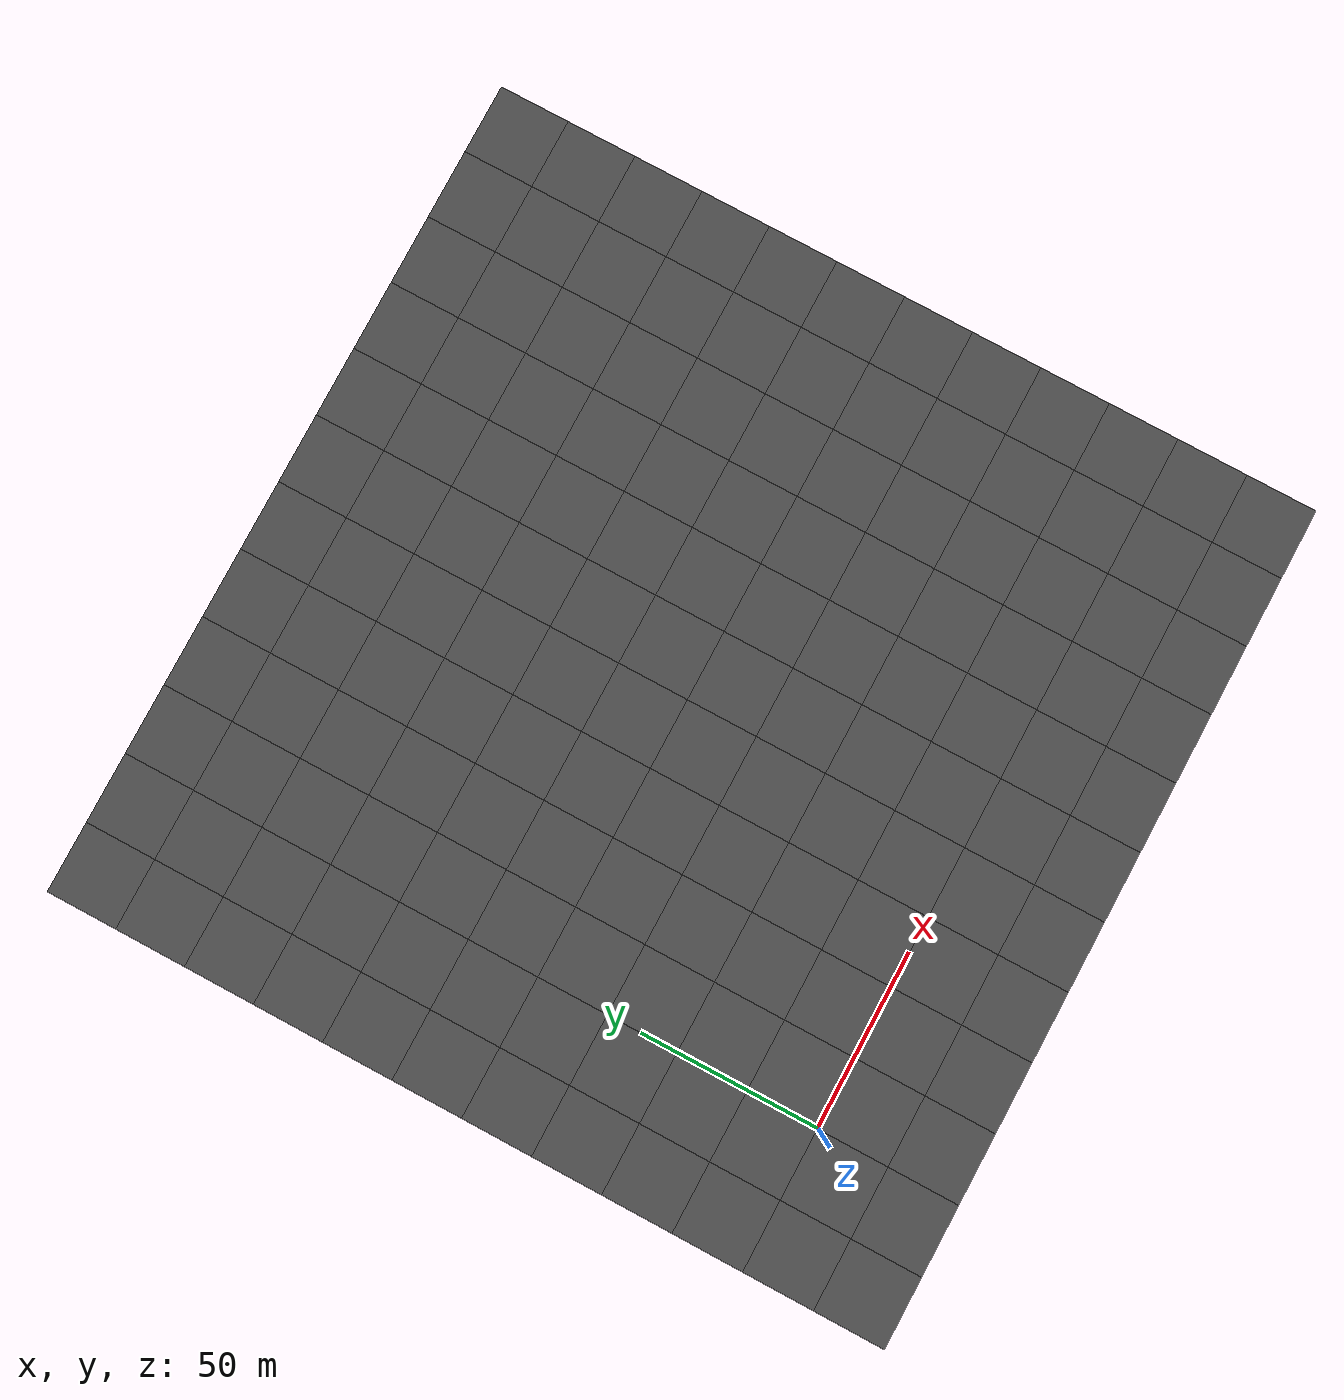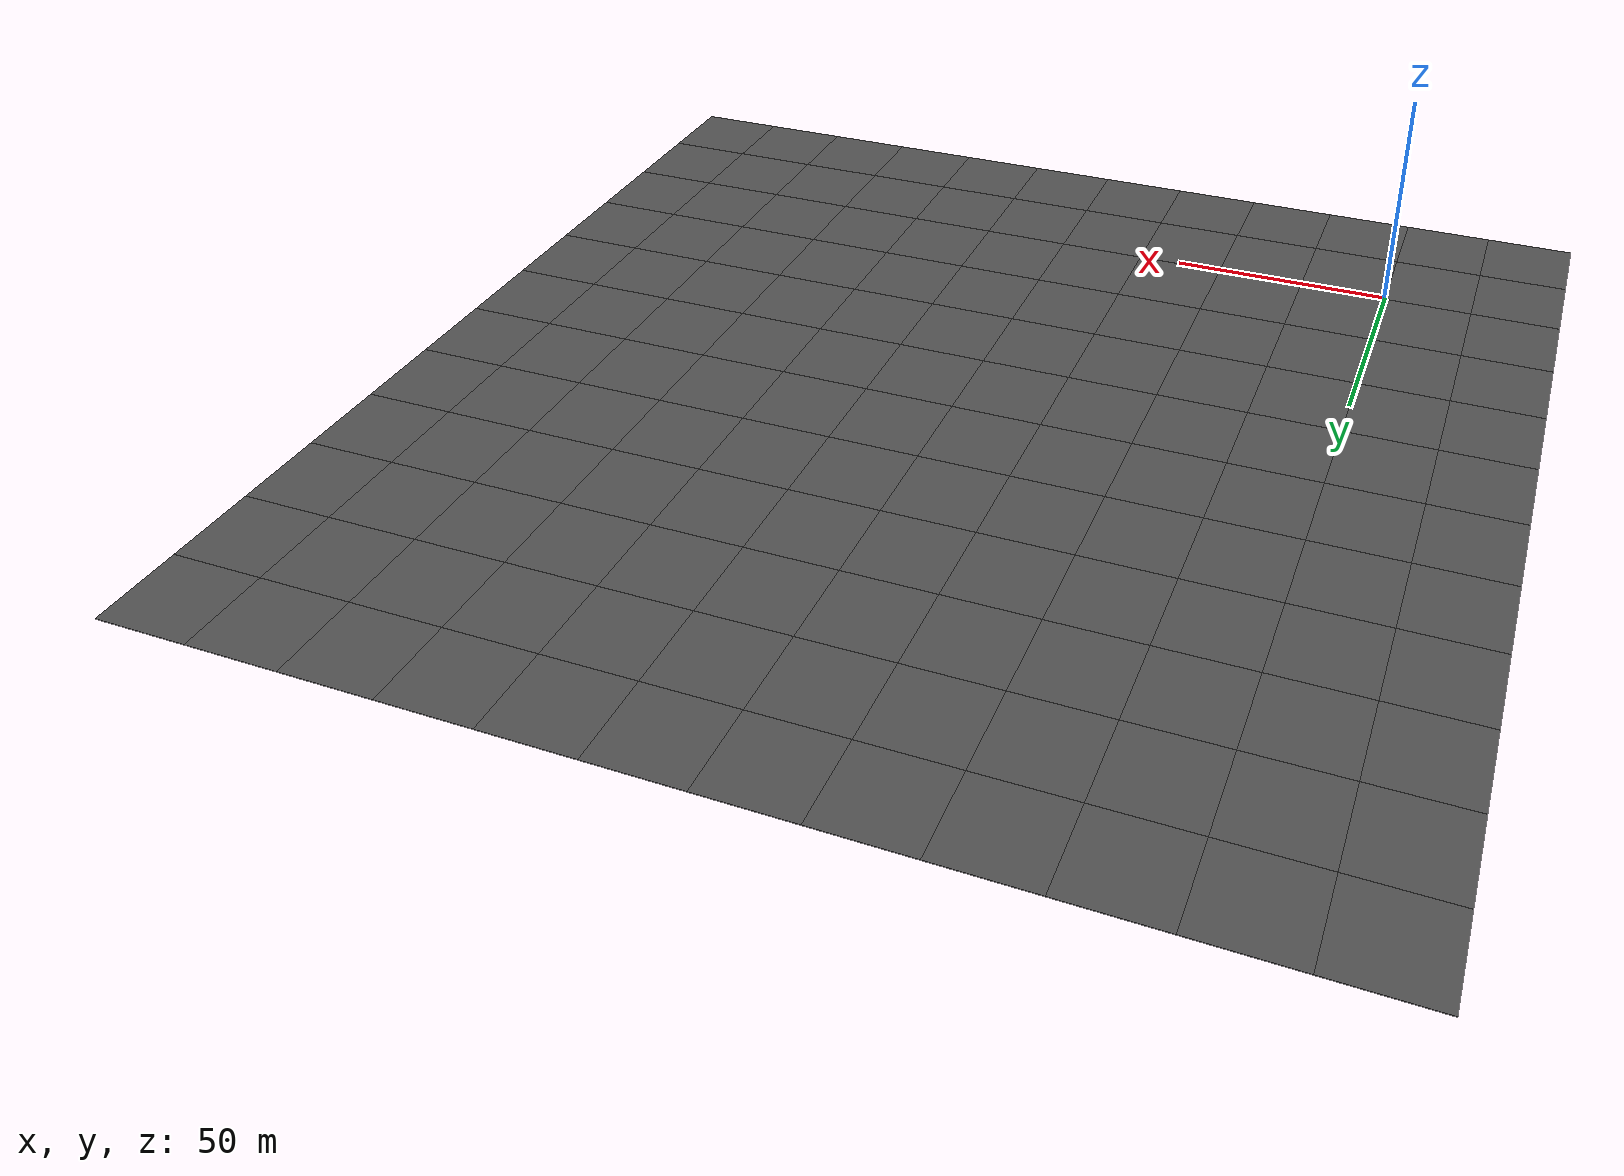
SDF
<sdf version="1.4">
 <world name="default">
  <plugin name="gazebo_octomap" filename="librotors_gazebo_octomap_plugin.so"/>
  <light name="sun" type="directional">
   <pose>0 0 10 0 0 0</pose>
   <diffuse>0.8 0.8 0.8 1</diffuse>
   <specular>0.2 0.2 0.2 1</specular>
   <attenuation>
    <range>1000</range>
    <constant>0.9</constant>
    <linear>0.01</linear>
    <quadratic>0.001</quadratic>
   </attenuation>
   <direction>-0.5 0.1 -0.9</direction>
  </light>
  <physics type="ode">
   <ode>
    <solver><type>quick</type><iters>1000</iters><sor>1.3</sor></solver>
    <constraints>
     <cfm>0</cfm>
     <erp>0.2</erp>
     <contact_max_correcting_vel>100</contact_max_correcting_vel>
     <contact_surface_layer>0.001</contact_surface_layer>
    </constraints>
   </ode>
   <max_step_size>0.005</max_step_size>
   <real_time_factor>1</real_time_factor>
   <real_time_update_rate>200</real_time_update_rate>
   <gravity>0 0 -9.8</gravity>
  </physics>
  <scene><ambient>0.4 0.4 0.4 1</ambient><background>0.7 0.7 0.7 1</background><shadows>1</shadows></scene>
  <spherical_coordinates>
   <surface_model>EARTH_WGS84</surface_model>
   <latitude_deg>0</latitude_deg>
   <longitude_deg>0</longitude_deg>
   <elevation>0</elevation>
   <heading_deg>0</heading_deg>
  </spherical_coordinates>
  <model name="asphalt_plane">
   <static>1</static>
   <link name="link">
    <collision name="collision"><geometry><box><size>20 20 0.1</size></box></geometry></collision>
    <visual name="visual">
     <cast_shadows>0</cast_shadows>
     <geometry><box><size>20 20 0.1</size></box></geometry>
     <material>
      <script>
       <uri>model://asphalt_plane/materials/scripts</uri>
       <uri>model://asphalt_plane/materials/textures</uri>
       <name>vrc/asphalt</name>
      </script>
     </material>
    </visual>
    <velocity_decay><linear>0</linear><angular>0</angular></velocity_decay>
   </link>
   <pose>-30 -30 0 0 0 0</pose>
  </model>
  <model name="asphalt_plane">
   <static>1</static>
   <link name="link">
    <collision name="collision"><geometry><box><size>20 20 0.1</size></box></geometry></collision>
    <visual name="visual">
     <cast_shadows>0</cast_shadows>
     <geometry><box><size>20 20 0.1</size></box></geometry>
     <material>
      <script>
       <uri>model://asphalt_plane/materials/scripts</uri>
       <uri>model://asphalt_plane/materials/textures</uri>
       <name>vrc/asphalt</name>
      </script>
     </material>
    </visual>
    <velocity_decay><linear>0</linear><angular>0</angular></velocity_decay>
   </link>
   <pose>-30 -10 0 0 0 0</pose>
  </model>
  <model name="asphalt_plane">
   <static>1</static>
   <link name="link">
    <collision name="collision"><geometry><box><size>20 20 0.1</size></box></geometry></collision>
    <visual name="visual">
     <cast_shadows>0</cast_shadows>
     <geometry><box><size>20 20 0.1</size></box></geometry>
     <material>
      <script>
       <uri>model://asphalt_plane/materials/scripts</uri>
       <uri>model://asphalt_plane/materials/textures</uri>
       <name>vrc/asphalt</name>
      </script>
     </material>
    </visual>
    <velocity_decay><linear>0</linear><angular>0</angular></velocity_decay>
   </link>
   <pose>-30 10 0 0 0 0</pose>
  </model>
  <model name="asphalt_plane">
   <static>1</static>
   <link name="link">
    <collision name="collision"><geometry><box><size>20 20 0.1</size></box></geometry></collision>
    <visual name="visual">
     <cast_shadows>0</cast_shadows>
     <geometry><box><size>20 20 0.1</size></box></geometry>
     <material>
      <script>
       <uri>model://asphalt_plane/materials/scripts</uri>
       <uri>model://asphalt_plane/materials/textures</uri>
       <name>vrc/asphalt</name>
      </script>
     </material>
    </visual>
    <velocity_decay><linear>0</linear><angular>0</angular></velocity_decay>
   </link>
   <pose>-30 30 0 0 0 0</pose>
  </model>
  <model name="asphalt_plane">
   <static>1</static>
   <link name="link">
    <collision name="collision"><geometry><box><size>20 20 0.1</size></box></geometry></collision>
    <visual name="visual">
     <cast_shadows>0</cast_shadows>
     <geometry><box><size>20 20 0.1</size></box></geometry>
     <material>
      <script>
       <uri>model://asphalt_plane/materials/scripts</uri>
       <uri>model://asphalt_plane/materials/textures</uri>
       <name>vrc/asphalt</name>
      </script>
     </material>
    </visual>
    <velocity_decay><linear>0</linear><angular>0</angular></velocity_decay>
   </link>
   <pose>-30 50 0 0 0 0</pose>
  </model>
  <model name="asphalt_plane">
   <static>1</static>
   <link name="link">
    <collision name="collision"><geometry><box><size>20 20 0.1</size></box></geometry></collision>
    <visual name="visual">
     <cast_shadows>0</cast_shadows>
     <geometry><box><size>20 20 0.1</size></box></geometry>
     <material>
      <script>
       <uri>model://asphalt_plane/materials/scripts</uri>
       <uri>model://asphalt_plane/materials/textures</uri>
       <name>vrc/asphalt</name>
      </script>
     </material>
    </visual>
    <velocity_decay><linear>0</linear><angular>0</angular></velocity_decay>
   </link>
   <pose>-30 70 0 0 0 0</pose>
  </model>
  <model name="asphalt_plane">
   <static>1</static>
   <link name="link">
    <collision name="collision"><geometry><box><size>20 20 0.1</size></box></geometry></collision>
    <visual name="visual">
     <cast_shadows>0</cast_shadows>
     <geometry><box><size>20 20 0.1</size></box></geometry>
     <material>
      <script>
       <uri>model://asphalt_plane/materials/scripts</uri>
       <uri>model://asphalt_plane/materials/textures</uri>
       <name>vrc/asphalt</name>
      </script>
     </material>
    </visual>
    <velocity_decay><linear>0</linear><angular>0</angular></velocity_decay>
   </link>
   <pose>-30 90 0 0 0 0</pose>
  </model>
  <model name="asphalt_plane">
   <static>1</static>
   <link name="link">
    <collision name="collision"><geometry><box><size>20 20 0.1</size></box></geometry></collision>
    <visual name="visual">
     <cast_shadows>0</cast_shadows>
     <geometry><box><size>20 20 0.1</size></box></geometry>
     <material>
      <script>
       <uri>model://asphalt_plane/materials/scripts</uri>
       <uri>model://asphalt_plane/materials/textures</uri>
       <name>vrc/asphalt</name>
      </script>
     </material>
    </visual>
    <velocity_decay><linear>0</linear><angular>0</angular></velocity_decay>
   </link>
   <pose>-30 110 0 0 0 0</pose>
  </model>
  <model name="asphalt_plane">
   <static>1</static>
   <link name="link">
    <collision name="collision"><geometry><box><size>20 20 0.1</size></box></geometry></collision>
    <visual name="visual">
     <cast_shadows>0</cast_shadows>
     <geometry><box><size>20 20 0.1</size></box></geometry>
     <material>
      <script>
       <uri>model://asphalt_plane/materials/scripts</uri>
       <uri>model://asphalt_plane/materials/textures</uri>
       <name>vrc/asphalt</name>
      </script>
     </material>
    </visual>
    <velocity_decay><linear>0</linear><angular>0</angular></velocity_decay>
   </link>
   <pose>-30 130 0 0 0 0</pose>
  </model>
  <model name="asphalt_plane">
   <static>1</static>
   <link name="link">
    <collision name="collision"><geometry><box><size>20 20 0.1</size></box></geometry></collision>
    <visual name="visual">
     <cast_shadows>0</cast_shadows>
     <geometry><box><size>20 20 0.1</size></box></geometry>
     <material>
      <script>
       <uri>model://asphalt_plane/materials/scripts</uri>
       <uri>model://asphalt_plane/materials/textures</uri>
       <name>vrc/asphalt</name>
      </script>
     </material>
    </visual>
    <velocity_decay><linear>0</linear><angular>0</angular></velocity_decay>
   </link>
   <pose>-30 150 0 0 0 0</pose>
  </model>
  <model name="asphalt_plane">
   <static>1</static>
   <link name="link">
    <collision name="collision"><geometry><box><size>20 20 0.1</size></box></geometry></collision>
    <visual name="visual">
     <cast_shadows>0</cast_shadows>
     <geometry><box><size>20 20 0.1</size></box></geometry>
     <material>
      <script>
       <uri>model://asphalt_plane/materials/scripts</uri>
       <uri>model://asphalt_plane/materials/textures</uri>
       <name>vrc/asphalt</name>
      </script>
     </material>
    </visual>
    <velocity_decay><linear>0</linear><angular>0</angular></velocity_decay>
   </link>
   <pose>-30 170 0 0 0 0</pose>
  </model>
  <model name="asphalt_plane">
   <static>1</static>
   <link name="link">
    <collision name="collision"><geometry><box><size>20 20 0.1</size></box></geometry></collision>
    <visual name="visual">
     <cast_shadows>0</cast_shadows>
     <geometry><box><size>20 20 0.1</size></box></geometry>
     <material>
      <script>
       <uri>model://asphalt_plane/materials/scripts</uri>
       <uri>model://asphalt_plane/materials/textures</uri>
       <name>vrc/asphalt</name>
      </script>
     </material>
    </visual>
    <velocity_decay><linear>0</linear><angular>0</angular></velocity_decay>
   </link>
   <pose>-30 190 0 0 0 0</pose>
  </model>
  <model name="asphalt_plane">
   <static>1</static>
   <link name="link">
    <collision name="collision"><geometry><box><size>20 20 0.1</size></box></geometry></collision>
    <visual name="visual">
     <cast_shadows>0</cast_shadows>
     <geometry><box><size>20 20 0.1</size></box></geometry>
     <material>
      <script>
       <uri>model://asphalt_plane/materials/scripts</uri>
       <uri>model://asphalt_plane/materials/textures</uri>
       <name>vrc/asphalt</name>
      </script>
     </material>
    </visual>
    <velocity_decay><linear>0</linear><angular>0</angular></velocity_decay>
   </link>
   <pose>-10 -30 0 0 0 0</pose>
  </model>
  <model name="asphalt_plane">
   <static>1</static>
   <link name="link">
    <collision name="collision"><geometry><box><size>20 20 0.1</size></box></geometry></collision>
    <visual name="visual">
     <cast_shadows>0</cast_shadows>
     <geometry><box><size>20 20 0.1</size></box></geometry>
     <material>
      <script>
       <uri>model://asphalt_plane/materials/scripts</uri>
       <uri>model://asphalt_plane/materials/textures</uri>
       <name>vrc/asphalt</name>
      </script>
     </material>
    </visual>
    <velocity_decay><linear>0</linear><angular>0</angular></velocity_decay>
   </link>
   <pose>-10 -10 0 0 0 0</pose>
  </model>
  <model name="asphalt_plane">
   <static>1</static>
   <link name="link">
    <collision name="collision"><geometry><box><size>20 20 0.1</size></box></geometry></collision>
    <visual name="visual">
     <cast_shadows>0</cast_shadows>
     <geometry><box><size>20 20 0.1</size></box></geometry>
     <material>
      <script>
       <uri>model://asphalt_plane/materials/scripts</uri>
       <uri>model://asphalt_plane/materials/textures</uri>
       <name>vrc/asphalt</name>
      </script>
     </material>
    </visual>
    <velocity_decay><linear>0</linear><angular>0</angular></velocity_decay>
   </link>
   <pose>-10 10 0 0 0 0</pose>
  </model>
  <model name="asphalt_plane">
   <static>1</static>
   <link name="link">
    <collision name="collision"><geometry><box><size>20 20 0.1</size></box></geometry></collision>
    <visual name="visual">
     <cast_shadows>0</cast_shadows>
     <geometry><box><size>20 20 0.1</size></box></geometry>
     <material>
      <script>
       <uri>model://asphalt_plane/materials/scripts</uri>
       <uri>model://asphalt_plane/materials/textures</uri>
       <name>vrc/asphalt</name>
      </script>
     </material>
    </visual>
    <velocity_decay><linear>0</linear><angular>0</angular></velocity_decay>
   </link>
   <pose>-10 30 0 0 0 0</pose>
  </model>
  <model name="asphalt_plane">
   <static>1</static>
   <link name="link">
    <collision name="collision"><geometry><box><size>20 20 0.1</size></box></geometry></collision>
    <visual name="visual">
     <cast_shadows>0</cast_shadows>
     <geometry><box><size>20 20 0.1</size></box></geometry>
     <material>
      <script>
       <uri>model://asphalt_plane/materials/scripts</uri>
       <uri>model://asphalt_plane/materials/textures</uri>
       <name>vrc/asphalt</name>
      </script>
     </material>
    </visual>
    <velocity_decay><linear>0</linear><angular>0</angular></velocity_decay>
   </link>
   <pose>-10 50 0 0 0 0</pose>
  </model>
  <model name="asphalt_plane">
   <static>1</static>
   <link name="link">
    <collision name="collision"><geometry><box><size>20 20 0.1</size></box></geometry></collision>
    <visual name="visual">
     <cast_shadows>0</cast_shadows>
     <geometry><box><size>20 20 0.1</size></box></geometry>
     <material>
      <script>
       <uri>model://asphalt_plane/materials/scripts</uri>
       <uri>model://asphalt_plane/materials/textures</uri>
       <name>vrc/asphalt</name>
      </script>
     </material>
    </visual>
    <velocity_decay><linear>0</linear><angular>0</angular></velocity_decay>
   </link>
   <pose>-10 70 0 0 0 0</pose>
  </model>
  <model name="asphalt_plane">
   <static>1</static>
   <link name="link">
    <collision name="collision"><geometry><box><size>20 20 0.1</size></box></geometry></collision>
    <visual name="visual">
     <cast_shadows>0</cast_shadows>
     <geometry><box><size>20 20 0.1</size></box></geometry>
     <material>
      <script>
       <uri>model://asphalt_plane/materials/scripts</uri>
       <uri>model://asphalt_plane/materials/textures</uri>
       <name>vrc/asphalt</name>
      </script>
     </material>
    </visual>
    <velocity_decay><linear>0</linear><angular>0</angular></velocity_decay>
   </link>
   <pose>-10 90 0 0 0 0</pose>
  </model>
  <model name="asphalt_plane">
   <static>1</static>
   <link name="link">
    <collision name="collision"><geometry><box><size>20 20 0.1</size></box></geometry></collision>
    <visual name="visual">
     <cast_shadows>0</cast_shadows>
     <geometry><box><size>20 20 0.1</size></box></geometry>
     <material>
      <script>
       <uri>model://asphalt_plane/materials/scripts</uri>
       <uri>model://asphalt_plane/materials/textures</uri>
       <name>vrc/asphalt</name>
      </script>
     </material>
    </visual>
    <velocity_decay><linear>0</linear><angular>0</angular></velocity_decay>
   </link>
   <pose>-10 110 0 0 0 0</pose>
  </model>
  <model name="asphalt_plane">
   <static>1</static>
   <link name="link">
    <collision name="collision"><geometry><box><size>20 20 0.1</size></box></geometry></collision>
    <visual name="visual">
     <cast_shadows>0</cast_shadows>
     <geometry><box><size>20 20 0.1</size></box></geometry>
     <material>
      <script>
       <uri>model://asphalt_plane/materials/scripts</uri>
       <uri>model://asphalt_plane/materials/textures</uri>
       <name>vrc/asphalt</name>
      </script>
     </material>
    </visual>
    <velocity_decay><linear>0</linear><angular>0</angular></velocity_decay>
   </link>
   <pose>-10 130 0 0 0 0</pose>
  </model>
  <model name="asphalt_plane">
   <static>1</static>
   <link name="link">
    <collision name="collision"><geometry><box><size>20 20 0.1</size></box></geometry></collision>
    <visual name="visual">
     <cast_shadows>0</cast_shadows>
     <geometry><box><size>20 20 0.1</size></box></geometry>
     <material>
      <script>
       <uri>model://asphalt_plane/materials/scripts</uri>
       <uri>model://asphalt_plane/materials/textures</uri>
       <name>vrc/asphalt</name>
      </script>
     </material>
    </visual>
    <velocity_decay><linear>0</linear><angular>0</angular></velocity_decay>
   </link>
   <pose>-10 150 0 0 0 0</pose>
  </model>
  <model name="asphalt_plane">
   <static>1</static>
   <link name="link">
    <collision name="collision"><geometry><box><size>20 20 0.1</size></box></geometry></collision>
    <visual name="visual">
     <cast_shadows>0</cast_shadows>
     <geometry><box><size>20 20 0.1</size></box></geometry>
     <material>
      <script>
       <uri>model://asphalt_plane/materials/scripts</uri>
       <uri>model://asphalt_plane/materials/textures</uri>
       <name>vrc/asphalt</name>
      </script>
     </material>
    </visual>
    <velocity_decay><linear>0</linear><angular>0</angular></velocity_decay>
   </link>
   <pose>-10 170 0 0 0 0</pose>
  </model>
  <model name="asphalt_plane">
   <static>1</static>
   <link name="link">
    <collision name="collision"><geometry><box><size>20 20 0.1</size></box></geometry></collision>
    <visual name="visual">
     <cast_shadows>0</cast_shadows>
     <geometry><box><size>20 20 0.1</size></box></geometry>
     <material>
      <script>
       <uri>model://asphalt_plane/materials/scripts</uri>
       <uri>model://asphalt_plane/materials/textures</uri>
       <name>vrc/asphalt</name>
      </script>
     </material>
    </visual>
    <velocity_decay><linear>0</linear><angular>0</angular></velocity_decay>
   </link>
   <pose>-10 190 0 0 0 0</pose>
  </model>
  <model name="asphalt_plane">
   <static>1</static>
   <link name="link">
    <collision name="collision"><geometry><box><size>20 20 0.1</size></box></geometry></collision>
    <visual name="visual">
     <cast_shadows>0</cast_shadows>
     <geometry><box><size>20 20 0.1</size></box></geometry>
     <material>
      <script>
       <uri>model://asphalt_plane/materials/scripts</uri>
       <uri>model://asphalt_plane/materials/textures</uri>
       <name>vrc/asphalt</name>
      </script>
     </material>
    </visual>
    <velocity_decay><linear>0</linear><angular>0</angular></velocity_decay>
   </link>
   <pose>10 -30 0 0 0 0</pose>
  </model>
  <model name="asphalt_plane">
   <static>1</static>
   <link name="link">
    <collision name="collision"><geometry><box><size>20 20 0.1</size></box></geometry></collision>
    <visual name="visual">
     <cast_shadows>0</cast_shadows>
     <geometry><box><size>20 20 0.1</size></box></geometry>
     <material>
      <script>
       <uri>model://asphalt_plane/materials/scripts</uri>
       <uri>model://asphalt_plane/materials/textures</uri>
       <name>vrc/asphalt</name>
      </script>
     </material>
    </visual>
    <velocity_decay><linear>0</linear><angular>0</angular></velocity_decay>
   </link>
   <pose>10 -10 0 0 0 0</pose>
  </model>
  <model name="asphalt_plane">
   <static>1</static>
   <link name="link">
    <collision name="collision"><geometry><box><size>20 20 0.1</size></box></geometry></collision>
    <visual name="visual">
     <cast_shadows>0</cast_shadows>
     <geometry><box><size>20 20 0.1</size></box></geometry>
     <material>
      <script>
       <uri>model://asphalt_plane/materials/scripts</uri>
       <uri>model://asphalt_plane/materials/textures</uri>
       <name>vrc/asphalt</name>
      </script>
     </material>
    </visual>
    <velocity_decay><linear>0</linear><angular>0</angular></velocity_decay>
   </link>
   <pose>10 10 0 0 0 0</pose>
  </model>
  <model name="asphalt_plane">
   <static>1</static>
   <link name="link">
    <collision name="collision"><geometry><box><size>20 20 0.1</size></box></geometry></collision>
    <visual name="visual">
     <cast_shadows>0</cast_shadows>
     <geometry><box><size>20 20 0.1</size></box></geometry>
     <material>
      <script>
       <uri>model://asphalt_plane/materials/scripts</uri>
       <uri>model://asphalt_plane/materials/textures</uri>
       <name>vrc/asphalt</name>
      </script>
     </material>
    </visual>
    <velocity_decay><linear>0</linear><angular>0</angular></velocity_decay>
   </link>
   <pose>10 30 0 0 0 0</pose>
  </model>
  <model name="asphalt_plane">
   <static>1</static>
   <link name="link">
    <collision name="collision"><geometry><box><size>20 20 0.1</size></box></geometry></collision>
    <visual name="visual">
     <cast_shadows>0</cast_shadows>
     <geometry><box><size>20 20 0.1</size></box></geometry>
     <material>
      <script>
       <uri>model://asphalt_plane/materials/scripts</uri>
       <uri>model://asphalt_plane/materials/textures</uri>
       <name>vrc/asphalt</name>
      </script>
     </material>
    </visual>
    <velocity_decay><linear>0</linear><angular>0</angular></velocity_decay>
   </link>
   <pose>10 50 0 0 0 0</pose>
  </model>
  <model name="asphalt_plane">
   <static>1</static>
   <link name="link">
    <collision name="collision"><geometry><box><size>20 20 0.1</size></box></geometry></collision>
    <visual name="visual">
     <cast_shadows>0</cast_shadows>
     <geometry><box><size>20 20 0.1</size></box></geometry>
     <material>
      <script>
       <uri>model://asphalt_plane/materials/scripts</uri>
       <uri>model://asphalt_plane/materials/textures</uri>
       <name>vrc/asphalt</name>
      </script>
     </material>
    </visual>
    <velocity_decay><linear>0</linear><angular>0</angular></velocity_decay>
   </link>
   <pose>10 70 0 0 0 0</pose>
  </model>
  <model name="asphalt_plane">
   <static>1</static>
   <link name="link">
    <collision name="collision"><geometry><box><size>20 20 0.1</size></box></geometry></collision>
    <visual name="visual">
     <cast_shadows>0</cast_shadows>
     <geometry><box><size>20 20 0.1</size></box></geometry>
     <material>
      <script>
       <uri>model://asphalt_plane/materials/scripts</uri>
       <uri>model://asphalt_plane/materials/textures</uri>
       <name>vrc/asphalt</name>
      </script>
     </material>
    </visual>
    <velocity_decay><linear>0</linear><angular>0</angular></velocity_decay>
   </link>
   <pose>10 90 0 0 0 0</pose>
  </model>
  <model name="asphalt_plane">
   <static>1</static>
   <link name="link">
    <collision name="collision"><geometry><box><size>20 20 0.1</size></box></geometry></collision>
    <visual name="visual">
     <cast_shadows>0</cast_shadows>
     <geometry><box><size>20 20 0.1</size></box></geometry>
     <material>
      <script>
       <uri>model://asphalt_plane/materials/scripts</uri>
       <uri>model://asphalt_plane/materials/textures</uri>
       <name>vrc/asphalt</name>
      </script>
     </material>
    </visual>
    <velocity_decay><linear>0</linear><angular>0</angular></velocity_decay>
   </link>
   <pose>10 110 0 0 0 0</pose>
  </model>
  <model name="asphalt_plane">
   <static>1</static>
   <link name="link">
    <collision name="collision"><geometry><box><size>20 20 0.1</size></box></geometry></collision>
    <visual name="visual">
     <cast_shadows>0</cast_shadows>
     <geometry><box><size>20 20 0.1</size></box></geometry>
     <material>
      <script>
       <uri>model://asphalt_plane/materials/scripts</uri>
       <uri>model://asphalt_plane/materials/textures</uri>
       <name>vrc/asphalt</name>
      </script>
     </material>
    </visual>
    <velocity_decay><linear>0</linear><angular>0</angular></velocity_decay>
   </link>
   <pose>10 130 0 0 0 0</pose>
  </model>
  <model name="asphalt_plane">
   <static>1</static>
   <link name="link">
    <collision name="collision"><geometry><box><size>20 20 0.1</size></box></geometry></collision>
    <visual name="visual">
     <cast_shadows>0</cast_shadows>
     <geometry><box><size>20 20 0.1</size></box></geometry>
     <material>
      <script>
       <uri>model://asphalt_plane/materials/scripts</uri>
       <uri>model://asphalt_plane/materials/textures</uri>
       <name>vrc/asphalt</name>
      </script>
     </material>
    </visual>
    <velocity_decay><linear>0</linear><angular>0</angular></velocity_decay>
   </link>
   <pose>10 150 0 0 0 0</pose>
  </model>
  <model name="asphalt_plane">
   <static>1</static>
   <link name="link">
    <collision name="collision"><geometry><box><size>20 20 0.1</size></box></geometry></collision>
    <visual name="visual">
     <cast_shadows>0</cast_shadows>
     <geometry><box><size>20 20 0.1</size></box></geometry>
     <material>
      <script>
       <uri>model://asphalt_plane/materials/scripts</uri>
       <uri>model://asphalt_plane/materials/textures</uri>
       <name>vrc/asphalt</name>
      </script>
     </material>
    </visual>
    <velocity_decay><linear>0</linear><angular>0</angular></velocity_decay>
   </link>
   <pose>10 170 0 0 0 0</pose>
  </model>
  <model name="asphalt_plane">
   <static>1</static>
   <link name="link">
    <collision name="collision"><geometry><box><size>20 20 0.1</size></box></geometry></collision>
    <visual name="visual">
     <cast_shadows>0</cast_shadows>
     <geometry><box><size>20 20 0.1</size></box></geometry>
     <material>
      <script>
       <uri>model://asphalt_plane/materials/scripts</uri>
       <uri>model://asphalt_plane/materials/textures</uri>
       <name>vrc/asphalt</name>
      </script>
     </material>
    </visual>
    <velocity_decay><linear>0</linear><angular>0</angular></velocity_decay>
   </link>
   <pose>10 190 0 0 0 0</pose>
  </model>
  <model name="asphalt_plane">
   <static>1</static>
   <link name="link">
    <collision name="collision"><geometry><box><size>20 20 0.1</size></box></geometry></collision>
    <visual name="visual">
     <cast_shadows>0</cast_shadows>
     <geometry><box><size>20 20 0.1</size></box></geometry>
     <material>
      <script>
       <uri>model://asphalt_plane/materials/scripts</uri>
       <uri>model://asphalt_plane/materials/textures</uri>
       <name>vrc/asphalt</name>
      </script>
     </material>
    </visual>
    <velocity_decay><linear>0</linear><angular>0</angular></velocity_decay>
   </link>
   <pose>30 -30 0 0 0 0</pose>
  </model>
  <model name="asphalt_plane">
   <static>1</static>
   <link name="link">
    <collision name="collision"><geometry><box><size>20 20 0.1</size></box></geometry></collision>
    <visual name="visual">
     <cast_shadows>0</cast_shadows>
     <geometry><box><size>20 20 0.1</size></box></geometry>
     <material>
      <script>
       <uri>model://asphalt_plane/materials/scripts</uri>
       <uri>model://asphalt_plane/materials/textures</uri>
       <name>vrc/asphalt</name>
      </script>
     </material>
    </visual>
    <velocity_decay><linear>0</linear><angular>0</angular></velocity_decay>
   </link>
   <pose>30 -10 0 0 0 0</pose>
  </model>
  <model name="asphalt_plane">
   <static>1</static>
   <link name="link">
    <collision name="collision"><geometry><box><size>20 20 0.1</size></box></geometry></collision>
    <visual name="visual">
     <cast_shadows>0</cast_shadows>
     <geometry><box><size>20 20 0.1</size></box></geometry>
     <material>
      <script>
       <uri>model://asphalt_plane/materials/scripts</uri>
       <uri>model://asphalt_plane/materials/textures</uri>
       <name>vrc/asphalt</name>
      </script>
     </material>
    </visual>
    <velocity_decay><linear>0</linear><angular>0</angular></velocity_decay>
   </link>
   <pose>30 10 0 0 0 0</pose>
  </model>
  <model name="asphalt_plane">
   <static>1</static>
   <link name="link">
    <collision name="collision"><geometry><box><size>20 20 0.1</size></box></geometry></collision>
    <visual name="visual">
     <cast_shadows>0</cast_shadows>
     <geometry><box><size>20 20 0.1</size></box></geometry>
     <material>
      <script>
       <uri>model://asphalt_plane/materials/scripts</uri>
       <uri>model://asphalt_plane/materials/textures</uri>
       <name>vrc/asphalt</name>
      </script>
     </material>
    </visual>
    <velocity_decay><linear>0</linear><angular>0</angular></velocity_decay>
   </link>
   <pose>30 30 0 0 0 0</pose>
  </model>
  <model name="asphalt_plane">
   <static>1</static>
   <link name="link">
    <collision name="collision"><geometry><box><size>20 20 0.1</size></box></geometry></collision>
    <visual name="visual">
     <cast_shadows>0</cast_shadows>
     <geometry><box><size>20 20 0.1</size></box></geometry>
     <material>
      <script>
       <uri>model://asphalt_plane/materials/scripts</uri>
       <uri>model://asphalt_plane/materials/textures</uri>
       <name>vrc/asphalt</name>
      </script>
     </material>
    </visual>
    <velocity_decay><linear>0</linear><angular>0</angular></velocity_decay>
   </link>
   <pose>30 50 0 0 0 0</pose>
  </model>
  <model name="asphalt_plane">
   <static>1</static>
   <link name="link">
    <collision name="collision"><geometry><box><size>20 20 0.1</size></box></geometry></collision>
    <visual name="visual">
     <cast_shadows>0</cast_shadows>
     <geometry><box><size>20 20 0.1</size></box></geometry>
     <material>
      <script>
       <uri>model://asphalt_plane/materials/scripts</uri>
       <uri>model://asphalt_plane/materials/textures</uri>
       <name>vrc/asphalt</name>
      </script>
     </material>
    </visual>
    <velocity_decay><linear>0</linear><angular>0</angular></velocity_decay>
   </link>
   <pose>30 70 0 0 0 0</pose>
  </model>
  <model name="asphalt_plane">
   <static>1</static>
   <link name="link">
    <collision name="collision"><geometry><box><size>20 20 0.1</size></box></geometry></collision>
    <visual name="visual">
     <cast_shadows>0</cast_shadows>
     <geometry><box><size>20 20 0.1</size></box></geometry>
     <material>
      <script>
       <uri>model://asphalt_plane/materials/scripts</uri>
       <uri>model://asphalt_plane/materials/textures</uri>
       <name>vrc/asphalt</name>
      </script>
     </material>
    </visual>
    <velocity_decay><linear>0</linear><angular>0</angular></velocity_decay>
   </link>
   <pose>30 90 0 0 0 0</pose>
  </model>
  <model name="asphalt_plane">
   <static>1</static>
   <link name="link">
    <collision name="collision"><geometry><box><size>20 20 0.1</size></box></geometry></collision>
    <visual name="visual">
     <cast_shadows>0</cast_shadows>
     <geometry><box><size>20 20 0.1</size></box></geometry>
     <material>
      <script>
       <uri>model://asphalt_plane/materials/scripts</uri>
       <uri>model://asphalt_plane/materials/textures</uri>
       <name>vrc/asphalt</name>
      </script>
     </material>
    </visual>
    <velocity_decay><linear>0</linear><angular>0</angular></velocity_decay>
   </link>
   <pose>30 110 0 0 0 0</pose>
  </model>
  <model name="asphalt_plane">
   <static>1</static>
   <link name="link">
    <collision name="collision"><geometry><box><size>20 20 0.1</size></box></geometry></collision>
    <visual name="visual">
     <cast_shadows>0</cast_shadows>
     <geometry><box><size>20 20 0.1</size></box></geometry>
     <material>
      <script>
       <uri>model://asphalt_plane/materials/scripts</uri>
       <uri>model://asphalt_plane/materials/textures</uri>
       <name>vrc/asphalt</name>
      </script>
     </material>
    </visual>
    <velocity_decay><linear>0</linear><angular>0</angular></velocity_decay>
   </link>
   <pose>30 130 0 0 0 0</pose>
  </model>
  <model name="asphalt_plane">
   <static>1</static>
   <link name="link">
    <collision name="collision"><geometry><box><size>20 20 0.1</size></box></geometry></collision>
    <visual name="visual">
     <cast_shadows>0</cast_shadows>
     <geometry><box><size>20 20 0.1</size></box></geometry>
     <material>
      <script>
       <uri>model://asphalt_plane/materials/scripts</uri>
       <uri>model://asphalt_plane/materials/textures</uri>
       <name>vrc/asphalt</name>
      </script>
     </material>
    </visual>
    <velocity_decay><linear>0</linear><angular>0</angular></velocity_decay>
   </link>
   <pose>30 150 0 0 0 0</pose>
  </model>
  <model name="asphalt_plane">
   <static>1</static>
   <link name="link">
    <collision name="collision"><geometry><box><size>20 20 0.1</size></box></geometry></collision>
    <visual name="visual">
     <cast_shadows>0</cast_shadows>
     <geometry><box><size>20 20 0.1</size></box></geometry>
     <material>
      <script>
       <uri>model://asphalt_plane/materials/scripts</uri>
       <uri>model://asphalt_plane/materials/textures</uri>
       <name>vrc/asphalt</name>
      </script>
     </material>
    </visual>
    <velocity_decay><linear>0</linear><angular>0</angular></velocity_decay>
   </link>
   <pose>30 170 0 0 0 0</pose>
  </model>
  <model name="asphalt_plane">
   <static>1</static>
   <link name="link">
    <collision name="collision"><geometry><box><size>20 20 0.1</size></box></geometry></collision>
    <visual name="visual">
     <cast_shadows>0</cast_shadows>
     <geometry><box><size>20 20 0.1</size></box></geometry>
     <material>
      <script>
       <uri>model://asphalt_plane/materials/scripts</uri>
       <uri>model://asphalt_plane/materials/textures</uri>
       <name>vrc/asphalt</name>
      </script>
     </material>
    </visual>
    <velocity_decay><linear>0</linear><angular>0</angular></velocity_decay>
   </link>
   <pose>30 190 0 0 0 0</pose>
  </model>
  <model name="asphalt_plane">
   <static>1</static>
   <link name="link">
    <collision name="collision"><geometry><box><size>20 20 0.1</size></box></geometry></collision>
    <visual name="visual">
     <cast_shadows>0</cast_shadows>
     <geometry><box><size>20 20 0.1</size></box></geometry>
     <material>
      <script>
       <uri>model://asphalt_plane/materials/scripts</uri>
       <uri>model://asphalt_plane/materials/textures</uri>
       <name>vrc/asphalt</name>
      </script>
     </material>
    </visual>
    <velocity_decay><linear>0</linear><angular>0</angular></velocity_decay>
   </link>
   <pose>50 -30 0 0 0 0</pose>
  </model>
  <model name="asphalt_plane">
   <static>1</static>
   <link name="link">
    <collision name="collision"><geometry><box><size>20 20 0.1</size></box></geometry></collision>
    <visual name="visual">
     <cast_shadows>0</cast_shadows>
     <geometry><box><size>20 20 0.1</size></box></geometry>
     <material>
      <script>
       <uri>model://asphalt_plane/materials/scripts</uri>
       <uri>model://asphalt_plane/materials/textures</uri>
       <name>vrc/asphalt</name>
      </script>
     </material>
    </visual>
    <velocity_decay><linear>0</linear><angular>0</angular></velocity_decay>
   </link>
   <pose>50 -10 0 0 0 0</pose>
  </model>
  <model name="asphalt_plane">
   <static>1</static>
   <link name="link">
    <collision name="collision"><geometry><box><size>20 20 0.1</size></box></geometry></collision>
    <visual name="visual">
     <cast_shadows>0</cast_shadows>
     <geometry><box><size>20 20 0.1</size></box></geometry>
     <material>
      <script>
       <uri>model://asphalt_plane/materials/scripts</uri>
       <uri>model://asphalt_plane/materials/textures</uri>
       <name>vrc/asphalt</name>
      </script>
     </material>
    </visual>
    <velocity_decay><linear>0</linear><angular>0</angular></velocity_decay>
   </link>
   <pose>50 10 0 0 0 0</pose>
  </model>
  <model name="asphalt_plane">
   <static>1</static>
   <link name="link">
    <collision name="collision"><geometry><box><size>20 20 0.1</size></box></geometry></collision>
    <visual name="visual">
     <cast_shadows>0</cast_shadows>
     <geometry><box><size>20 20 0.1</size></box></geometry>
     <material>
      <script>
       <uri>model://asphalt_plane/materials/scripts</uri>
       <uri>model://asphalt_plane/materials/textures</uri>
       <name>vrc/asphalt</name>
      </script>
     </material>
    </visual>
    <velocity_decay><linear>0</linear><angular>0</angular></velocity_decay>
   </link>
   <pose>50 30 0 0 0 0</pose>
  </model>
  <model name="asphalt_plane">
   <static>1</static>
   <link name="link">
    <collision name="collision"><geometry><box><size>20 20 0.1</size></box></geometry></collision>
    <visual name="visual">
     <cast_shadows>0</cast_shadows>
     <geometry><box><size>20 20 0.1</size></box></geometry>
     <material>
      <script>
       <uri>model://asphalt_plane/materials/scripts</uri>
       <uri>model://asphalt_plane/materials/textures</uri>
       <name>vrc/asphalt</name>
      </script>
     </material>
    </visual>
    <velocity_decay><linear>0</linear><angular>0</angular></velocity_decay>
   </link>
   <pose>50 50 0 0 0 0</pose>
  </model>
  <model name="asphalt_plane">
   <static>1</static>
   <link name="link">
    <collision name="collision"><geometry><box><size>20 20 0.1</size></box></geometry></collision>
    <visual name="visual">
     <cast_shadows>0</cast_shadows>
     <geometry><box><size>20 20 0.1</size></box></geometry>
     <material>
      <script>
       <uri>model://asphalt_plane/materials/scripts</uri>
       <uri>model://asphalt_plane/materials/textures</uri>
       <name>vrc/asphalt</name>
      </script>
     </material>
    </visual>
    <velocity_decay><linear>0</linear><angular>0</angular></velocity_decay>
   </link>
   <pose>50 70 0 0 0 0</pose>
  </model>
  <model name="asphalt_plane">
   <static>1</static>
   <link name="link">
    <collision name="collision"><geometry><box><size>20 20 0.1</size></box></geometry></collision>
    <visual name="visual">
     <cast_shadows>0</cast_shadows>
     <geometry><box><size>20 20 0.1</size></box></geometry>
     <material>
      <script>
       <uri>model://asphalt_plane/materials/scripts</uri>
       <uri>model://asphalt_plane/materials/textures</uri>
       <name>vrc/asphalt</name>
      </script>
     </material>
    </visual>
    <velocity_decay><linear>0</linear><angular>0</angular></velocity_decay>
   </link>
   <pose>50 90 0 0 0 0</pose>
  </model>
  <model name="asphalt_plane">
   <static>1</static>
   <link name="link">
    <collision name="collision"><geometry><box><size>20 20 0.1</size></box></geometry></collision>
    <visual name="visual">
     <cast_shadows>0</cast_shadows>
     <geometry><box><size>20 20 0.1</size></box></geometry>
     <material>
      <script>
       <uri>model://asphalt_plane/materials/scripts</uri>
       <uri>model://asphalt_plane/materials/textures</uri>
       <name>vrc/asphalt</name>
      </script>
     </material>
    </visual>
    <velocity_decay><linear>0</linear><angular>0</angular></velocity_decay>
   </link>
   <pose>50 110 0 0 0 0</pose>
  </model>
  <model name="asphalt_plane">
   <static>1</static>
   <link name="link">
    <collision name="collision"><geometry><box><size>20 20 0.1</size></box></geometry></collision>
    <visual name="visual">
     <cast_shadows>0</cast_shadows>
     <geometry><box><size>20 20 0.1</size></box></geometry>
     <material>
      <script>
       <uri>model://asphalt_plane/materials/scripts</uri>
       <uri>model://asphalt_plane/materials/textures</uri>
       <name>vrc/asphalt</name>
      </script>
     </material>
    </visual>
    <velocity_decay><linear>0</linear><angular>0</angular></velocity_decay>
   </link>
   <pose>50 130 0 0 0 0</pose>
  </model>
  <model name="asphalt_plane">
   <static>1</static>
   <link name="link">
    <collision name="collision"><geometry><box><size>20 20 0.1</size></box></geometry></collision>
    <visual name="visual">
     <cast_shadows>0</cast_shadows>
     <geometry><box><size>20 20 0.1</size></box></geometry>
     <material>
      <script>
       <uri>model://asphalt_plane/materials/scripts</uri>
       <uri>model://asphalt_plane/materials/textures</uri>
       <name>vrc/asphalt</name>
      </script>
     </material>
    </visual>
    <velocity_decay><linear>0</linear><angular>0</angular></velocity_decay>
   </link>
   <pose>50 150 0 0 0 0</pose>
  </model>
  <model name="asphalt_plane">
   <static>1</static>
   <link name="link">
    <collision name="collision"><geometry><box><size>20 20 0.1</size></box></geometry></collision>
    <visual name="visual">
     <cast_shadows>0</cast_shadows>
     <geometry><box><size>20 20 0.1</size></box></geometry>
     <material>
      <script>
       <uri>model://asphalt_plane/materials/scripts</uri>
       <uri>model://asphalt_plane/materials/textures</uri>
       <name>vrc/asphalt</name>
      </script>
     </material>
    </visual>
    <velocity_decay><linear>0</linear><angular>0</angular></velocity_decay>
   </link>
   <pose>50 170 0 0 0 0</pose>
  </model>
  <model name="asphalt_plane">
   <static>1</static>
   <link name="link">
    <collision name="collision"><geometry><box><size>20 20 0.1</size></box></geometry></collision>
    <visual name="visual">
     <cast_shadows>0</cast_shadows>
     <geometry><box><size>20 20 0.1</size></box></geometry>
     <material>
      <script>
       <uri>model://asphalt_plane/materials/scripts</uri>
       <uri>model://asphalt_plane/materials/textures</uri>
       <name>vrc/asphalt</name>
      </script>
     </material>
    </visual>
    <velocity_decay><linear>0</linear><angular>0</angular></velocity_decay>
   </link>
   <pose>50 190 0 0 0 0</pose>
  </model>
  <model name="asphalt_plane">
   <static>1</static>
   <link name="link">
    <collision name="collision"><geometry><box><size>20 20 0.1</size></box></geometry></collision>
    <visual name="visual">
     <cast_shadows>0</cast_shadows>
     <geometry><box><size>20 20 0.1</size></box></geometry>
     <material>
      <script>
       <uri>model://asphalt_plane/materials/scripts</uri>
       <uri>model://asphalt_plane/materials/textures</uri>
       <name>vrc/asphalt</name>
      </script>
     </material>
    </visual>
    <velocity_decay><linear>0</linear><angular>0</angular></velocity_decay>
   </link>
   <pose>70 -30 0 0 0 0</pose>
  </model>
  <model name="asphalt_plane">
   <static>1</static>
   <link name="link">
    <collision name="collision"><geometry><box><size>20 20 0.1</size></box></geometry></collision>
    <visual name="visual">
     <cast_shadows>0</cast_shadows>
     <geometry><box><size>20 20 0.1</size></box></geometry>
     <material>
      <script>
       <uri>model://asphalt_plane/materials/scripts</uri>
       <uri>model://asphalt_plane/materials/textures</uri>
       <name>vrc/asphalt</name>
      </script>
     </material>
    </visual>
    <velocity_decay><linear>0</linear><angular>0</angular></velocity_decay>
   </link>
   <pose>70 -10 0 0 0 0</pose>
  </model>
  <model name="asphalt_plane">
   <static>1</static>
   <link name="link">
    <collision name="collision"><geometry><box><size>20 20 0.1</size></box></geometry></collision>
    <visual name="visual">
     <cast_shadows>0</cast_shadows>
     <geometry><box><size>20 20 0.1</size></box></geometry>
     <material>
      <script>
       <uri>model://asphalt_plane/materials/scripts</uri>
       <uri>model://asphalt_plane/materials/textures</uri>
       <name>vrc/asphalt</name>
      </script>
     </material>
    </visual>
    <velocity_decay><linear>0</linear><angular>0</angular></velocity_decay>
   </link>
   <pose>70 10 0 0 0 0</pose>
  </model>
  <model name="asphalt_plane">
   <static>1</static>
   <link name="link">
    <collision name="collision"><geometry><box><size>20 20 0.1</size></box></geometry></collision>
    <visual name="visual">
     <cast_shadows>0</cast_shadows>
     <geometry><box><size>20 20 0.1</size></box></geometry>
     <material>
      <script>
       <uri>model://asphalt_plane/materials/scripts</uri>
       <uri>model://asphalt_plane/materials/textures</uri>
       <name>vrc/asphalt</name>
      </script>
     </material>
    </visual>
    <velocity_decay><linear>0</linear><angular>0</angular></velocity_decay>
   </link>
   <pose>70 30 0 0 0 0</pose>
  </model>
  <model name="asphalt_plane">
   <static>1</static>
   <link name="link">
    <collision name="collision"><geometry><box><size>20 20 0.1</size></box></geometry></collision>
    <visual name="visual">
     <cast_shadows>0</cast_shadows>
     <geometry><box><size>20 20 0.1</size></box></geometry>
     <material>
      <script>
       <uri>model://asphalt_plane/materials/scripts</uri>
       <uri>model://asphalt_plane/materials/textures</uri>
       <name>vrc/asphalt</name>
      </script>
     </material>
    </visual>
    <velocity_decay><linear>0</linear><angular>0</angular></velocity_decay>
   </link>
   <pose>70 50 0 0 0 0</pose>
  </model>
  <model name="asphalt_plane">
   <static>1</static>
   <link name="link">
    <collision name="collision"><geometry><box><size>20 20 0.1</size></box></geometry></collision>
    <visual name="visual">
     <cast_shadows>0</cast_shadows>
     <geometry><box><size>20 20 0.1</size></box></geometry>
     <material>
      <script>
       <uri>model://asphalt_plane/materials/scripts</uri>
       <uri>model://asphalt_plane/materials/textures</uri>
       <name>vrc/asphalt</name>
      </script>
     </material>
    </visual>
    <velocity_decay><linear>0</linear><angular>0</angular></velocity_decay>
   </link>
   <pose>70 70 0 0 0 0</pose>
  </model>
  <model name="asphalt_plane">
   <static>1</static>
   <link name="link">
    <collision name="collision"><geometry><box><size>20 20 0.1</size></box></geometry></collision>
    <visual name="visual">
     <cast_shadows>0</cast_shadows>
     <geometry><box><size>20 20 0.1</size></box></geometry>
     <material>
      <script>
       <uri>model://asphalt_plane/materials/scripts</uri>
       <uri>model://asphalt_plane/materials/textures</uri>
       <name>vrc/asphalt</name>
      </script>
     </material>
    </visual>
    <velocity_decay><linear>0</linear><angular>0</angular></velocity_decay>
   </link>
   <pose>70 90 0 0 0 0</pose>
  </model>
  <model name="asphalt_plane">
   <static>1</static>
   <link name="link">
    <collision name="collision"><geometry><box><size>20 20 0.1</size></box></geometry></collision>
    <visual name="visual">
     <cast_shadows>0</cast_shadows>
     <geometry><box><size>20 20 0.1</size></box></geometry>
     <material>
      <script>
       <uri>model://asphalt_plane/materials/scripts</uri>
       <uri>model://asphalt_plane/materials/textures</uri>
       <name>vrc/asphalt</name>
      </script>
     </material>
    </visual>
    <velocity_decay><linear>0</linear><angular>0</angular></velocity_decay>
   </link>
   <pose>70 110 0 0 0 0</pose>
  </model>
  <model name="asphalt_plane">
   <static>1</static>
   <link name="link">
    <collision name="collision"><geometry><box><size>20 20 0.1</size></box></geometry></collision>
    <visual name="visual">
     <cast_shadows>0</cast_shadows>
     <geometry><box><size>20 20 0.1</size></box></geometry>
     <material>
      <script>
       <uri>model://asphalt_plane/materials/scripts</uri>
       <uri>model://asphalt_plane/materials/textures</uri>
       <name>vrc/asphalt</name>
      </script>
     </material>
    </visual>
    <velocity_decay><linear>0</linear><angular>0</angular></velocity_decay>
   </link>
   <pose>70 130 0 0 0 0</pose>
  </model>
  <model name="asphalt_plane">
   <static>1</static>
   <link name="link">
    <collision name="collision"><geometry><box><size>20 20 0.1</size></box></geometry></collision>
    <visual name="visual">
     <cast_shadows>0</cast_shadows>
     <geometry><box><size>20 20 0.1</size></box></geometry>
     <material>
      <script>
       <uri>model://asphalt_plane/materials/scripts</uri>
       <uri>model://asphalt_plane/materials/textures</uri>
       <name>vrc/asphalt</name>
      </script>
     </material>
    </visual>
    <velocity_decay><linear>0</linear><angular>0</angular></velocity_decay>
   </link>
   <pose>70 150 0 0 0 0</pose>
  </model>
  <model name="asphalt_plane">
   <static>1</static>
   <link name="link">
    <collision name="collision"><geometry><box><size>20 20 0.1</size></box></geometry></collision>
    <visual name="visual">
     <cast_shadows>0</cast_shadows>
     <geometry><box><size>20 20 0.1</size></box></geometry>
     <material>
      <script>
       <uri>model://asphalt_plane/materials/scripts</uri>
       <uri>model://asphalt_plane/materials/textures</uri>
       <name>vrc/asphalt</name>
      </script>
     </material>
    </visual>
    <velocity_decay><linear>0</linear><angular>0</angular></velocity_decay>
   </link>
   <pose>70 170 0 0 0 0</pose>
  </model>
  <model name="asphalt_plane">
   <static>1</static>
   <link name="link">
    <collision name="collision"><geometry><box><size>20 20 0.1</size></box></geometry></collision>
    <visual name="visual">
     <cast_shadows>0</cast_shadows>
     <geometry><box><size>20 20 0.1</size></box></geometry>
     <material>
      <script>
       <uri>model://asphalt_plane/materials/scripts</uri>
       <uri>model://asphalt_plane/materials/textures</uri>
       <name>vrc/asphalt</name>
      </script>
     </material>
    </visual>
    <velocity_decay><linear>0</linear><angular>0</angular></velocity_decay>
   </link>
   <pose>70 190 0 0 0 0</pose>
  </model>
  <model name="asphalt_plane">
   <static>1</static>
   <link name="link">
    <collision name="collision"><geometry><box><size>20 20 0.1</size></box></geometry></collision>
    <visual name="visual">
     <cast_shadows>0</cast_shadows>
     <geometry><box><size>20 20 0.1</size></box></geometry>
     <material>
      <script>
       <uri>model://asphalt_plane/materials/scripts</uri>
       <uri>model://asphalt_plane/materials/textures</uri>
       <name>vrc/asphalt</name>
      </script>
     </material>
    </visual>
    <velocity_decay><linear>0</linear><angular>0</angular></velocity_decay>
   </link>
   <pose>90 -30 0 0 0 0</pose>
  </model>
  <model name="asphalt_plane">
   <static>1</static>
   <link name="link">
    <collision name="collision"><geometry><box><size>20 20 0.1</size></box></geometry></collision>
    <visual name="visual">
     <cast_shadows>0</cast_shadows>
     <geometry><box><size>20 20 0.1</size></box></geometry>
     <material>
      <script>
       <uri>model://asphalt_plane/materials/scripts</uri>
       <uri>model://asphalt_plane/materials/textures</uri>
       <name>vrc/asphalt</name>
      </script>
     </material>
    </visual>
    <velocity_decay><linear>0</linear><angular>0</angular></velocity_decay>
   </link>
   <pose>90 -10 0 0 0 0</pose>
  </model>
  <model name="asphalt_plane">
   <static>1</static>
   <link name="link">
    <collision name="collision"><geometry><box><size>20 20 0.1</size></box></geometry></collision>
    <visual name="visual">
     <cast_shadows>0</cast_shadows>
     <geometry><box><size>20 20 0.1</size></box></geometry>
     <material>
      <script>
       <uri>model://asphalt_plane/materials/scripts</uri>
       <uri>model://asphalt_plane/materials/textures</uri>
       <name>vrc/asphalt</name>
      </script>
     </material>
    </visual>
    <velocity_decay><linear>0</linear><angular>0</angular></velocity_decay>
   </link>
   <pose>90 10 0 0 0 0</pose>
  </model>
  <model name="asphalt_plane">
   <static>1</static>
   <link name="link">
    <collision name="collision"><geometry><box><size>20 20 0.1</size></box></geometry></collision>
    <visual name="visual">
     <cast_shadows>0</cast_shadows>
     <geometry><box><size>20 20 0.1</size></box></geometry>
     <material>
      <script>
       <uri>model://asphalt_plane/materials/scripts</uri>
       <uri>model://asphalt_plane/materials/textures</uri>
       <name>vrc/asphalt</name>
      </script>
     </material>
    </visual>
    <velocity_decay><linear>0</linear><angular>0</angular></velocity_decay>
   </link>
   <pose>90 30 0 0 0 0</pose>
  </model>
  <model name="asphalt_plane">
   <static>1</static>
   <link name="link">
    <collision name="collision"><geometry><box><size>20 20 0.1</size></box></geometry></collision>
    <visual name="visual">
     <cast_shadows>0</cast_shadows>
     <geometry><box><size>20 20 0.1</size></box></geometry>
     <material>
      <script>
       <uri>model://asphalt_plane/materials/scripts</uri>
       <uri>model://asphalt_plane/materials/textures</uri>
       <name>vrc/asphalt</name>
      </script>
     </material>
    </visual>
    <velocity_decay><linear>0</linear><angular>0</angular></velocity_decay>
   </link>
   <pose>90 50 0 0 0 0</pose>
  </model>
  <model name="asphalt_plane">
   <static>1</static>
   <link name="link">
    <collision name="collision"><geometry><box><size>20 20 0.1</size></box></geometry></collision>
    <visual name="visual">
     <cast_shadows>0</cast_shadows>
     <geometry><box><size>20 20 0.1</size></box></geometry>
     <material>
      <script>
       <uri>model://asphalt_plane/materials/scripts</uri>
       <uri>model://asphalt_plane/materials/textures</uri>
       <name>vrc/asphalt</name>
      </script>
     </material>
    </visual>
    <velocity_decay><linear>0</linear><angular>0</angular></velocity_decay>
   </link>
   <pose>90 70 0 0 0 0</pose>
  </model>
  <model name="asphalt_plane">
   <static>1</static>
   <link name="link">
    <collision name="collision"><geometry><box><size>20 20 0.1</size></box></geometry></collision>
    <visual name="visual">
     <cast_shadows>0</cast_shadows>
     <geometry><box><size>20 20 0.1</size></box></geometry>
     <material>
      <script>
       <uri>model://asphalt_plane/materials/scripts</uri>
       <uri>model://asphalt_plane/materials/textures</uri>
       <name>vrc/asphalt</name>
      </script>
     </material>
    </visual>
    <velocity_decay><linear>0</linear><angular>0</angular></velocity_decay>
   </link>
   <pose>90 90 0 0 0 0</pose>
  </model>
  <model name="asphalt_plane">
   <static>1</static>
   <link name="link">
    <collision name="collision"><geometry><box><size>20 20 0.1</size></box></geometry></collision>
    <visual name="visual">
     <cast_shadows>0</cast_shadows>
     <geometry><box><size>20 20 0.1</size></box></geometry>
     <material>
      <script>
       <uri>model://asphalt_plane/materials/scripts</uri>
       <uri>model://asphalt_plane/materials/textures</uri>
       <name>vrc/asphalt</name>
      </script>
     </material>
    </visual>
    <velocity_decay><linear>0</linear><angular>0</angular></velocity_decay>
   </link>
   <pose>90 110 0 0 0 0</pose>
  </model>
  <model name="asphalt_plane">
   <static>1</static>
   <link name="link">
    <collision name="collision"><geometry><box><size>20 20 0.1</size></box></geometry></collision>
    <visual name="visual">
     <cast_shadows>0</cast_shadows>
     <geometry><box><size>20 20 0.1</size></box></geometry>
     <material>
      <script>
       <uri>model://asphalt_plane/materials/scripts</uri>
       <uri>model://asphalt_plane/materials/textures</uri>
       <name>vrc/asphalt</name>
      </script>
     </material>
    </visual>
    <velocity_decay><linear>0</linear><angular>0</angular></velocity_decay>
   </link>
   <pose>90 130 0 0 0 0</pose>
  </model>
  <model name="asphalt_plane">
   <static>1</static>
   <link name="link">
    <collision name="collision"><geometry><box><size>20 20 0.1</size></box></geometry></collision>
    <visual name="visual">
     <cast_shadows>0</cast_shadows>
     <geometry><box><size>20 20 0.1</size></box></geometry>
     <material>
      <script>
       <uri>model://asphalt_plane/materials/scripts</uri>
       <uri>model://asphalt_plane/materials/textures</uri>
       <name>vrc/asphalt</name>
      </script>
     </material>
    </visual>
    <velocity_decay><linear>0</linear><angular>0</angular></velocity_decay>
   </link>
   <pose>90 150 0 0 0 0</pose>
  </model>
  <model name="asphalt_plane">
   <static>1</static>
   <link name="link">
    <collision name="collision"><geometry><box><size>20 20 0.1</size></box></geometry></collision>
    <visual name="visual">
     <cast_shadows>0</cast_shadows>
     <geometry><box><size>20 20 0.1</size></box></geometry>
     <material>
      <script>
       <uri>model://asphalt_plane/materials/scripts</uri>
       <uri>model://asphalt_plane/materials/textures</uri>
       <name>vrc/asphalt</name>
      </script>
     </material>
    </visual>
    <velocity_decay><linear>0</linear><angular>0</angular></velocity_decay>
   </link>
   <pose>90 170 0 0 0 0</pose>
  </model>
  <model name="asphalt_plane">
   <static>1</static>
   <link name="link">
    <collision name="collision"><geometry><box><size>20 20 0.1</size></box></geometry></collision>
    <visual name="visual">
     <cast_shadows>0</cast_shadows>
     <geometry><box><size>20 20 0.1</size></box></geometry>
     <material>
      <script>
       <uri>model://asphalt_plane/materials/scripts</uri>
       <uri>model://asphalt_plane/materials/textures</uri>
       <name>vrc/asphalt</name>
      </script>
     </material>
    </visual>
    <velocity_decay><linear>0</linear><angular>0</angular></velocity_decay>
   </link>
   <pose>90 190 0 0 0 0</pose>
  </model>
  <model name="asphalt_plane">
   <static>1</static>
   <link name="link">
    <collision name="collision"><geometry><box><size>20 20 0.1</size></box></geometry></collision>
    <visual name="visual">
     <cast_shadows>0</cast_shadows>
     <geometry><box><size>20 20 0.1</size></box></geometry>
     <material>
      <script>
       <uri>model://asphalt_plane/materials/scripts</uri>
       <uri>model://asphalt_plane/materials/textures</uri>
       <name>vrc/asphalt</name>
      </script>
     </material>
    </visual>
    <velocity_decay><linear>0</linear><angular>0</angular></velocity_decay>
   </link>
   <pose>110 -30 0 0 0 0</pose>
  </model>
  <model name="asphalt_plane">
   <static>1</static>
   <link name="link">
    <collision name="collision"><geometry><box><size>20 20 0.1</size></box></geometry></collision>
    <visual name="visual">
     <cast_shadows>0</cast_shadows>
     <geometry><box><size>20 20 0.1</size></box></geometry>
     <material>
      <script>
       <uri>model://asphalt_plane/materials/scripts</uri>
       <uri>model://asphalt_plane/materials/textures</uri>
       <name>vrc/asphalt</name>
      </script>
     </material>
    </visual>
    <velocity_decay><linear>0</linear><angular>0</angular></velocity_decay>
   </link>
   <pose>110 -10 0 0 0 0</pose>
  </model>
  <model name="asphalt_plane">
   <static>1</static>
   <link name="link">
    <collision name="collision"><geometry><box><size>20 20 0.1</size></box></geometry></collision>
    <visual name="visual">
     <cast_shadows>0</cast_shadows>
     <geometry><box><size>20 20 0.1</size></box></geometry>
     <material>
      <script>
       <uri>model://asphalt_plane/materials/scripts</uri>
       <uri>model://asphalt_plane/materials/textures</uri>
       <name>vrc/asphalt</name>
      </script>
     </material>
    </visual>
    <velocity_decay><linear>0</linear><angular>0</angular></velocity_decay>
   </link>
   <pose>110 10 0 0 0 0</pose>
  </model>
  <model name="asphalt_plane">
   <static>1</static>
   <link name="link">
    <collision name="collision"><geometry><box><size>20 20 0.1</size></box></geometry></collision>
    <visual name="visual">
     <cast_shadows>0</cast_shadows>
     <geometry><box><size>20 20 0.1</size></box></geometry>
     <material>
      <script>
       <uri>model://asphalt_plane/materials/scripts</uri>
       <uri>model://asphalt_plane/materials/textures</uri>
       <name>vrc/asphalt</name>
      </script>
     </material>
    </visual>
    <velocity_decay><linear>0</linear><angular>0</angular></velocity_decay>
   </link>
   <pose>110 30 0 0 0 0</pose>
  </model>
  <model name="asphalt_plane">
   <static>1</static>
   <link name="link">
    <collision name="collision"><geometry><box><size>20 20 0.1</size></box></geometry></collision>
    <visual name="visual">
     <cast_shadows>0</cast_shadows>
     <geometry><box><size>20 20 0.1</size></box></geometry>
     <material>
      <script>
       <uri>model://asphalt_plane/materials/scripts</uri>
       <uri>model://asphalt_plane/materials/textures</uri>
       <name>vrc/asphalt</name>
      </script>
     </material>
    </visual>
    <velocity_decay><linear>0</linear><angular>0</angular></velocity_decay>
   </link>
   <pose>110 50 0 0 0 0</pose>
  </model>
  <model name="asphalt_plane">
   <static>1</static>
   <link name="link">
    <collision name="collision"><geometry><box><size>20 20 0.1</size></box></geometry></collision>
    <visual name="visual">
     <cast_shadows>0</cast_shadows>
     <geometry><box><size>20 20 0.1</size></box></geometry>
     <material>
      <script>
       <uri>model://asphalt_plane/materials/scripts</uri>
       <uri>model://asphalt_plane/materials/textures</uri>
       <name>vrc/asphalt</name>
      </script>
     </material>
    </visual>
    <velocity_decay><linear>0</linear><angular>0</angular></velocity_decay>
   </link>
   <pose>110 70 0 0 0 0</pose>
  </model>
  <model name="asphalt_plane">
   <static>1</static>
   <link name="link">
    <collision name="collision"><geometry><box><size>20 20 0.1</size></box></geometry></collision>
    <visual name="visual">
     <cast_shadows>0</cast_shadows>
     <geometry><box><size>20 20 0.1</size></box></geometry>
     <material>
      <script>
       <uri>model://asphalt_plane/materials/scripts</uri>
       <uri>model://asphalt_plane/materials/textures</uri>
       <name>vrc/asphalt</name>
      </script>
     </material>
    </visual>
    <velocity_decay><linear>0</linear><angular>0</angular></velocity_decay>
   </link>
   <pose>110 90 0 0 0 0</pose>
  </model>
  <model name="asphalt_plane">
   <static>1</static>
   <link name="link">
    <collision name="collision"><geometry><box><size>20 20 0.1</size></box></geometry></collision>
    <visual name="visual">
     <cast_shadows>0</cast_shadows>
     <geometry><box><size>20 20 0.1</size></box></geometry>
     <material>
      <script>
       <uri>model://asphalt_plane/materials/scripts</uri>
       <uri>model://asphalt_plane/materials/textures</uri>
       <name>vrc/asphalt</name>
      </script>
     </material>
    </visual>
    <velocity_decay><linear>0</linear><angular>0</angular></velocity_decay>
   </link>
   <pose>110 110 0 0 0 0</pose>
  </model>
  <model name="asphalt_plane">
   <static>1</static>
   <link name="link">
    <collision name="collision"><geometry><box><size>20 20 0.1</size></box></geometry></collision>
    <visual name="visual">
     <cast_shadows>0</cast_shadows>
     <geometry><box><size>20 20 0.1</size></box></geometry>
     <material>
      <script>
       <uri>model://asphalt_plane/materials/scripts</uri>
       <uri>model://asphalt_plane/materials/textures</uri>
       <name>vrc/asphalt</name>
      </script>
     </material>
    </visual>
    <velocity_decay><linear>0</linear><angular>0</angular></velocity_decay>
   </link>
   <pose>110 130 0 0 0 0</pose>
  </model>
  <model name="asphalt_plane">
   <static>1</static>
   <link name="link">
    <collision name="collision"><geometry><box><size>20 20 0.1</size></box></geometry></collision>
    <visual name="visual">
     <cast_shadows>0</cast_shadows>
     <geometry><box><size>20 20 0.1</size></box></geometry>
     <material>
      <script>
       <uri>model://asphalt_plane/materials/scripts</uri>
       <uri>model://asphalt_plane/materials/textures</uri>
       <name>vrc/asphalt</name>
      </script>
     </material>
    </visual>
    <velocity_decay><linear>0</linear><angular>0</angular></velocity_decay>
   </link>
   <pose>110 150 0 0 0 0</pose>
  </model>
  <model name="asphalt_plane">
   <static>1</static>
   <link name="link">
    <collision name="collision"><geometry><box><size>20 20 0.1</size></box></geometry></collision>
    <visual name="visual">
     <cast_shadows>0</cast_shadows>
     <geometry><box><size>20 20 0.1</size></box></geometry>
     <material>
      <script>
       <uri>model://asphalt_plane/materials/scripts</uri>
       <uri>model://asphalt_plane/materials/textures</uri>
       <name>vrc/asphalt</name>
      </script>
     </material>
    </visual>
    <velocity_decay><linear>0</linear><angular>0</angular></velocity_decay>
   </link>
   <pose>110 170 0 0 0 0</pose>
  </model>
  <model name="asphalt_plane">
   <static>1</static>
   <link name="link">
    <collision name="collision"><geometry><box><size>20 20 0.1</size></box></geometry></collision>
    <visual name="visual">
     <cast_shadows>0</cast_shadows>
     <geometry><box><size>20 20 0.1</size></box></geometry>
     <material>
      <script>
       <uri>model://asphalt_plane/materials/scripts</uri>
       <uri>model://asphalt_plane/materials/textures</uri>
       <name>vrc/asphalt</name>
      </script>
     </material>
    </visual>
    <velocity_decay><linear>0</linear><angular>0</angular></velocity_decay>
   </link>
   <pose>110 190 0 0 0 0</pose>
  </model>
  <model name="asphalt_plane">
   <static>1</static>
   <link name="link">
    <collision name="collision"><geometry><box><size>20 20 0.1</size></box></geometry></collision>
    <visual name="visual">
     <cast_shadows>0</cast_shadows>
     <geometry><box><size>20 20 0.1</size></box></geometry>
     <material>
      <script>
       <uri>model://asphalt_plane/materials/scripts</uri>
       <uri>model://asphalt_plane/materials/textures</uri>
       <name>vrc/asphalt</name>
      </script>
     </material>
    </visual>
    <velocity_decay><linear>0</linear><angular>0</angular></velocity_decay>
   </link>
   <pose>130 -30 0 0 0 0</pose>
  </model>
  <model name="asphalt_plane">
   <static>1</static>
   <link name="link">
    <collision name="collision"><geometry><box><size>20 20 0.1</size></box></geometry></collision>
    <visual name="visual">
     <cast_shadows>0</cast_shadows>
     <geometry><box><size>20 20 0.1</size></box></geometry>
     <material>
      <script>
       <uri>model://asphalt_plane/materials/scripts</uri>
       <uri>model://asphalt_plane/materials/textures</uri>
       <name>vrc/asphalt</name>
      </script>
     </material>
    </visual>
    <velocity_decay><linear>0</linear><angular>0</angular></velocity_decay>
   </link>
   <pose>130 -10 0 0 0 0</pose>
  </model>
  <model name="asphalt_plane">
   <static>1</static>
   <link name="link">
    <collision name="collision"><geometry><box><size>20 20 0.1</size></box></geometry></collision>
    <visual name="visual">
     <cast_shadows>0</cast_shadows>
     <geometry><box><size>20 20 0.1</size></box></geometry>
     <material>
      <script>
       <uri>model://asphalt_plane/materials/scripts</uri>
       <uri>model://asphalt_plane/materials/textures</uri>
       <name>vrc/asphalt</name>
      </script>
     </material>
    </visual>
    <velocity_decay><linear>0</linear><angular>0</angular></velocity_decay>
   </link>
   <pose>130 10 0 0 0 0</pose>
  </model>
  <model name="asphalt_plane">
   <static>1</static>
   <link name="link">
    <collision name="collision"><geometry><box><size>20 20 0.1</size></box></geometry></collision>
    <visual name="visual">
     <cast_shadows>0</cast_shadows>
     <geometry><box><size>20 20 0.1</size></box></geometry>
     <material>
      <script>
       <uri>model://asphalt_plane/materials/scripts</uri>
       <uri>model://asphalt_plane/materials/textures</uri>
       <name>vrc/asphalt</name>
      </script>
     </material>
    </visual>
    <velocity_decay><linear>0</linear><angular>0</angular></velocity_decay>
   </link>
   <pose>130 30 0 0 0 0</pose>
  </model>
  <model name="asphalt_plane">
   <static>1</static>
   <link name="link">
    <collision name="collision"><geometry><box><size>20 20 0.1</size></box></geometry></collision>
    <visual name="visual">
     <cast_shadows>0</cast_shadows>
     <geometry><box><size>20 20 0.1</size></box></geometry>
     <material>
      <script>
       <uri>model://asphalt_plane/materials/scripts</uri>
       <uri>model://asphalt_plane/materials/textures</uri>
       <name>vrc/asphalt</name>
      </script>
     </material>
    </visual>
    <velocity_decay><linear>0</linear><angular>0</angular></velocity_decay>
   </link>
   <pose>130 50 0 0 0 0</pose>
  </model>
  <model name="asphalt_plane">
   <static>1</static>
   <link name="link">
    <collision name="collision"><geometry><box><size>20 20 0.1</size></box></geometry></collision>
    <visual name="visual">
     <cast_shadows>0</cast_shadows>
     <geometry><box><size>20 20 0.1</size></box></geometry>
     <material>
      <script>
       <uri>model://asphalt_plane/materials/scripts</uri>
       <uri>model://asphalt_plane/materials/textures</uri>
       <name>vrc/asphalt</name>
      </script>
     </material>
    </visual>
    <velocity_decay><linear>0</linear><angular>0</angular></velocity_decay>
   </link>
   <pose>130 70 0 0 0 0</pose>
  </model>
  <model name="asphalt_plane">
   <static>1</static>
   <link name="link">
    <collision name="collision"><geometry><box><size>20 20 0.1</size></box></geometry></collision>
    <visual name="visual">
     <cast_shadows>0</cast_shadows>
     <geometry><box><size>20 20 0.1</size></box></geometry>
     <material>
      <script>
       <uri>model://asphalt_plane/materials/scripts</uri>
       <uri>model://asphalt_plane/materials/textures</uri>
       <name>vrc/asphalt</name>
      </script>
     </material>
    </visual>
    <velocity_decay><linear>0</linear><angular>0</angular></velocity_decay>
   </link>
   <pose>130 90 0 0 0 0</pose>
  </model>
  <model name="asphalt_plane">
   <static>1</static>
   <link name="link">
    <collision name="collision"><geometry><box><size>20 20 0.1</size></box></geometry></collision>
    <visual name="visual">
     <cast_shadows>0</cast_shadows>
     <geometry><box><size>20 20 0.1</size></box></geometry>
     <material>
      <script>
       <uri>model://asphalt_plane/materials/scripts</uri>
       <uri>model://asphalt_plane/materials/textures</uri>
       <name>vrc/asphalt</name>
      </script>
     </material>
    </visual>
    <velocity_decay><linear>0</linear><angular>0</angular></velocity_decay>
   </link>
   <pose>130 110 0 0 0 0</pose>
  </model>
  <model name="asphalt_plane">
   <static>1</static>
   <link name="link">
    <collision name="collision"><geometry><box><size>20 20 0.1</size></box></geometry></collision>
    <visual name="visual">
     <cast_shadows>0</cast_shadows>
     <geometry><box><size>20 20 0.1</size></box></geometry>
     <material>
      <script>
       <uri>model://asphalt_plane/materials/scripts</uri>
       <uri>model://asphalt_plane/materials/textures</uri>
       <name>vrc/asphalt</name>
      </script>
     </material>
    </visual>
    <velocity_decay><linear>0</linear><angular>0</angular></velocity_decay>
   </link>
   <pose>130 130 0 0 0 0</pose>
  </model>
  <model name="asphalt_plane">
   <static>1</static>
   <link name="link">
    <collision name="collision"><geometry><box><size>20 20 0.1</size></box></geometry></collision>
    <visual name="visual">
     <cast_shadows>0</cast_shadows>
     <geometry><box><size>20 20 0.1</size></box></geometry>
     <material>
      <script>
       <uri>model://asphalt_plane/materials/scripts</uri>
       <uri>model://asphalt_plane/materials/textures</uri>
       <name>vrc/asphalt</name>
      </script>
     </material>
    </visual>
    <velocity_decay><linear>0</linear><angular>0</angular></velocity_decay>
   </link>
   <pose>130 150 0 0 0 0</pose>
  </model>
  <model name="asphalt_plane">
   <static>1</static>
   <link name="link">
    <collision name="collision"><geometry><box><size>20 20 0.1</size></box></geometry></collision>
    <visual name="visual">
     <cast_shadows>0</cast_shadows>
     <geometry><box><size>20 20 0.1</size></box></geometry>
     <material>
      <script>
       <uri>model://asphalt_plane/materials/scripts</uri>
       <uri>model://asphalt_plane/materials/textures</uri>
       <name>vrc/asphalt</name>
      </script>
     </material>
    </visual>
    <velocity_decay><linear>0</linear><angular>0</angular></velocity_decay>
   </link>
   <pose>130 170 0 0 0 0</pose>
  </model>
  <model name="asphalt_plane">
   <static>1</static>
   <link name="link">
    <collision name="collision"><geometry><box><size>20 20 0.1</size></box></geometry></collision>
    <visual name="visual">
     <cast_shadows>0</cast_shadows>
     <geometry><box><size>20 20 0.1</size></box></geometry>
     <material>
      <script>
       <uri>model://asphalt_plane/materials/scripts</uri>
       <uri>model://asphalt_plane/materials/textures</uri>
       <name>vrc/asphalt</name>
      </script>
     </material>
    </visual>
    <velocity_decay><linear>0</linear><angular>0</angular></velocity_decay>
   </link>
   <pose>130 190 0 0 0 0</pose>
  </model>
  <model name="asphalt_plane">
   <static>1</static>
   <link name="link">
    <collision name="collision"><geometry><box><size>20 20 0.1</size></box></geometry></collision>
    <visual name="visual">
     <cast_shadows>0</cast_shadows>
     <geometry><box><size>20 20 0.1</size></box></geometry>
     <material>
      <script>
       <uri>model://asphalt_plane/materials/scripts</uri>
       <uri>model://asphalt_plane/materials/textures</uri>
       <name>vrc/asphalt</name>
      </script>
     </material>
    </visual>
    <velocity_decay><linear>0</linear><angular>0</angular></velocity_decay>
   </link>
   <pose>150 -30 0 0 0 0</pose>
  </model>
  <model name="asphalt_plane">
   <static>1</static>
   <link name="link">
    <collision name="collision"><geometry><box><size>20 20 0.1</size></box></geometry></collision>
    <visual name="visual">
     <cast_shadows>0</cast_shadows>
     <geometry><box><size>20 20 0.1</size></box></geometry>
     <material>
      <script>
       <uri>model://asphalt_plane/materials/scripts</uri>
       <uri>model://asphalt_plane/materials/textures</uri>
       <name>vrc/asphalt</name>
      </script>
     </material>
    </visual>
    <velocity_decay><linear>0</linear><angular>0</angular></velocity_decay>
   </link>
   <pose>150 -10 0 0 0 0</pose>
  </model>
  <model name="asphalt_plane">
   <static>1</static>
   <link name="link">
    <collision name="collision"><geometry><box><size>20 20 0.1</size></box></geometry></collision>
    <visual name="visual">
     <cast_shadows>0</cast_shadows>
     <geometry><box><size>20 20 0.1</size></box></geometry>
     <material>
      <script>
       <uri>model://asphalt_plane/materials/scripts</uri>
       <uri>model://asphalt_plane/materials/textures</uri>
       <name>vrc/asphalt</name>
      </script>
     </material>
    </visual>
    <velocity_decay><linear>0</linear><angular>0</angular></velocity_decay>
   </link>
   <pose>150 10 0 0 0 0</pose>
  </model>
  <model name="asphalt_plane">
   <static>1</static>
   <link name="link">
    <collision name="collision"><geometry><box><size>20 20 0.1</size></box></geometry></collision>
    <visual name="visual">
     <cast_shadows>0</cast_shadows>
     <geometry><box><size>20 20 0.1</size></box></geometry>
     <material>
      <script>
       <uri>model://asphalt_plane/materials/scripts</uri>
       <uri>model://asphalt_plane/materials/textures</uri>
       <name>vrc/asphalt</name>
      </script>
     </material>
    </visual>
    <velocity_decay><linear>0</linear><angular>0</angular></velocity_decay>
   </link>
   <pose>150 30 0 0 0 0</pose>
  </model>
  <model name="asphalt_plane">
   <static>1</static>
   <link name="link">
    <collision name="collision"><geometry><box><size>20 20 0.1</size></box></geometry></collision>
    <visual name="visual">
     <cast_shadows>0</cast_shadows>
     <geometry><box><size>20 20 0.1</size></box></geometry>
     <material>
      <script>
       <uri>model://asphalt_plane/materials/scripts</uri>
       <uri>model://asphalt_plane/materials/textures</uri>
       <name>vrc/asphalt</name>
      </script>
     </material>
    </visual>
    <velocity_decay><linear>0</linear><angular>0</angular></velocity_decay>
   </link>
   <pose>150 50 0 0 0 0</pose>
  </model>
  <model name="asphalt_plane">
   <static>1</static>
   <link name="link">
    <collision name="collision"><geometry><box><size>20 20 0.1</size></box></geometry></collision>
    <visual name="visual">
     <cast_shadows>0</cast_shadows>
     <geometry><box><size>20 20 0.1</size></box></geometry>
     <material>
      <script>
       <uri>model://asphalt_plane/materials/scripts</uri>
       <uri>model://asphalt_plane/materials/textures</uri>
       <name>vrc/asphalt</name>
      </script>
     </material>
    </visual>
    <velocity_decay><linear>0</linear><angular>0</angular></velocity_decay>
   </link>
   <pose>150 70 0 0 0 0</pose>
  </model>
  <model name="asphalt_plane">
   <static>1</static>
   <link name="link">
    <collision name="collision"><geometry><box><size>20 20 0.1</size></box></geometry></collision>
    <visual name="visual">
     <cast_shadows>0</cast_shadows>
     <geometry><box><size>20 20 0.1</size></box></geometry>
     <material>
      <script>
       <uri>model://asphalt_plane/materials/scripts</uri>
       <uri>model://asphalt_plane/materials/textures</uri>
       <name>vrc/asphalt</name>
      </script>
     </material>
    </visual>
    <velocity_decay><linear>0</linear><angular>0</angular></velocity_decay>
   </link>
   <pose>150 90 0 0 0 0</pose>
  </model>
  <model name="asphalt_plane">
   <static>1</static>
   <link name="link">
    <collision name="collision"><geometry><box><size>20 20 0.1</size></box></geometry></collision>
    <visual name="visual">
     <cast_shadows>0</cast_shadows>
     <geometry><box><size>20 20 0.1</size></box></geometry>
     <material>
      <script>
       <uri>model://asphalt_plane/materials/scripts</uri>
       <uri>model://asphalt_plane/materials/textures</uri>
       <name>vrc/asphalt</name>
      </script>
     </material>
    </visual>
    <velocity_decay><linear>0</linear><angular>0</angular></velocity_decay>
   </link>
   <pose>150 110 0 0 0 0</pose>
  </model>
  <model name="asphalt_plane">
   <static>1</static>
   <link name="link">
    <collision name="collision"><geometry><box><size>20 20 0.1</size></box></geometry></collision>
    <visual name="visual">
     <cast_shadows>0</cast_shadows>
     <geometry><box><size>20 20 0.1</size></box></geometry>
     <material>
      <script>
       <uri>model://asphalt_plane/materials/scripts</uri>
       <uri>model://asphalt_plane/materials/textures</uri>
       <name>vrc/asphalt</name>
      </script>
     </material>
    </visual>
    <velocity_decay><linear>0</linear><angular>0</angular></velocity_decay>
   </link>
   <pose>150 130 0 0 0 0</pose>
  </model>
  <model name="asphalt_plane">
   <static>1</static>
   <link name="link">
    <collision name="collision"><geometry><box><size>20 20 0.1</size></box></geometry></collision>
    <visual name="visual">
     <cast_shadows>0</cast_shadows>
     <geometry><box><size>20 20 0.1</size></box></geometry>
     <material>
      <script>
       <uri>model://asphalt_plane/materials/scripts</uri>
       <uri>model://asphalt_plane/materials/textures</uri>
       <name>vrc/asphalt</name>
      </script>
     </material>
    </visual>
    <velocity_decay><linear>0</linear><angular>0</angular></velocity_decay>
   </link>
   <pose>150 150 0 0 0 0</pose>
  </model>
  <model name="asphalt_plane">
   <static>1</static>
   <link name="link">
    <collision name="collision"><geometry><box><size>20 20 0.1</size></box></geometry></collision>
    <visual name="visual">
     <cast_shadows>0</cast_shadows>
     <geometry><box><size>20 20 0.1</size></box></geometry>
     <material>
      <script>
       <uri>model://asphalt_plane/materials/scripts</uri>
       <uri>model://asphalt_plane/materials/textures</uri>
       <name>vrc/asphalt</name>
      </script>
     </material>
    </visual>
    <velocity_decay><linear>0</linear><angular>0</angular></velocity_decay>
   </link>
   <pose>150 170 0 0 0 0</pose>
  </model>
  <model name="asphalt_plane">
   <static>1</static>
   <link name="link">
    <collision name="collision"><geometry><box><size>20 20 0.1</size></box></geometry></collision>
    <visual name="visual">
     <cast_shadows>0</cast_shadows>
     <geometry><box><size>20 20 0.1</size></box></geometry>
     <material>
      <script>
       <uri>model://asphalt_plane/materials/scripts</uri>
       <uri>model://asphalt_plane/materials/textures</uri>
       <name>vrc/asphalt</name>
      </script>
     </material>
    </visual>
    <velocity_decay><linear>0</linear><angular>0</angular></velocity_decay>
   </link>
   <pose>150 190 0 0 0 0</pose>
  </model>
  <model name="asphalt_plane">
   <static>1</static>
   <link name="link">
    <collision name="collision"><geometry><box><size>20 20 0.1</size></box></geometry></collision>
    <visual name="visual">
     <cast_shadows>0</cast_shadows>
     <geometry><box><size>20 20 0.1</size></box></geometry>
     <material>
      <script>
       <uri>model://asphalt_plane/materials/scripts</uri>
       <uri>model://asphalt_plane/materials/textures</uri>
       <name>vrc/asphalt</name>
      </script>
     </material>
    </visual>
    <velocity_decay><linear>0</linear><angular>0</angular></velocity_decay>
   </link>
   <pose>170 -30 0 0 0 0</pose>
  </model>
  <model name="asphalt_plane">
   <static>1</static>
   <link name="link">
    <collision name="collision"><geometry><box><size>20 20 0.1</size></box></geometry></collision>
    <visual name="visual">
     <cast_shadows>0</cast_shadows>
     <geometry><box><size>20 20 0.1</size></box></geometry>
     <material>
      <script>
       <uri>model://asphalt_plane/materials/scripts</uri>
       <uri>model://asphalt_plane/materials/textures</uri>
       <name>vrc/asphalt</name>
      </script>
     </material>
    </visual>
    <velocity_decay><linear>0</linear><angular>0</angular></velocity_decay>
   </link>
   <pose>170 -10 0 0 0 0</pose>
  </model>
  <model name="asphalt_plane">
   <static>1</static>
   <link name="link">
    <collision name="collision"><geometry><box><size>20 20 0.1</size></box></geometry></collision>
    <visual name="visual">
     <cast_shadows>0</cast_shadows>
     <geometry><box><size>20 20 0.1</size></box></geometry>
     <material>
      <script>
       <uri>model://asphalt_plane/materials/scripts</uri>
       <uri>model://asphalt_plane/materials/textures</uri>
       <name>vrc/asphalt</name>
      </script>
     </material>
    </visual>
    <velocity_decay><linear>0</linear><angular>0</angular></velocity_decay>
   </link>
   <pose>170 10 0 0 0 0</pose>
  </model>
  <model name="asphalt_plane">
   <static>1</static>
   <link name="link">
    <collision name="collision"><geometry><box><size>20 20 0.1</size></box></geometry></collision>
    <visual name="visual">
     <cast_shadows>0</cast_shadows>
     <geometry><box><size>20 20 0.1</size></box></geometry>
     <material>
      <script>
       <uri>model://asphalt_plane/materials/scripts</uri>
       <uri>model://asphalt_plane/materials/textures</uri>
       <name>vrc/asphalt</name>
      </script>
     </material>
    </visual>
    <velocity_decay><linear>0</linear><angular>0</angular></velocity_decay>
   </link>
   <pose>170 30 0 0 0 0</pose>
  </model>
  <model name="asphalt_plane">
   <static>1</static>
   <link name="link">
    <collision name="collision"><geometry><box><size>20 20 0.1</size></box></geometry></collision>
    <visual name="visual">
     <cast_shadows>0</cast_shadows>
     <geometry><box><size>20 20 0.1</size></box></geometry>
     <material>
      <script>
       <uri>model://asphalt_plane/materials/scripts</uri>
       <uri>model://asphalt_plane/materials/textures</uri>
       <name>vrc/asphalt</name>
      </script>
     </material>
    </visual>
    <velocity_decay><linear>0</linear><angular>0</angular></velocity_decay>
   </link>
   <pose>170 50 0 0 0 0</pose>
  </model>
  <model name="asphalt_plane">
   <static>1</static>
   <link name="link">
    <collision name="collision"><geometry><box><size>20 20 0.1</size></box></geometry></collision>
    <visual name="visual">
     <cast_shadows>0</cast_shadows>
     <geometry><box><size>20 20 0.1</size></box></geometry>
     <material>
      <script>
       <uri>model://asphalt_plane/materials/scripts</uri>
       <uri>model://asphalt_plane/materials/textures</uri>
       <name>vrc/asphalt</name>
      </script>
     </material>
    </visual>
    <velocity_decay><linear>0</linear><angular>0</angular></velocity_decay>
   </link>
   <pose>170 70 0 0 0 0</pose>
  </model>
  <model name="asphalt_plane">
   <static>1</static>
   <link name="link">
    <collision name="collision"><geometry><box><size>20 20 0.1</size></box></geometry></collision>
    <visual name="visual">
     <cast_shadows>0</cast_shadows>
     <geometry><box><size>20 20 0.1</size></box></geometry>
     <material>
      <script>
       <uri>model://asphalt_plane/materials/scripts</uri>
       <uri>model://asphalt_plane/materials/textures</uri>
       <name>vrc/asphalt</name>
      </script>
     </material>
    </visual>
    <velocity_decay><linear>0</linear><angular>0</angular></velocity_decay>
   </link>
   <pose>170 90 0 0 0 0</pose>
  </model>
  <model name="asphalt_plane">
   <static>1</static>
   <link name="link">
    <collision name="collision"><geometry><box><size>20 20 0.1</size></box></geometry></collision>
    <visual name="visual">
     <cast_shadows>0</cast_shadows>
     <geometry><box><size>20 20 0.1</size></box></geometry>
     <material>
      <script>
       <uri>model://asphalt_plane/materials/scripts</uri>
       <uri>model://asphalt_plane/materials/textures</uri>
       <name>vrc/asphalt</name>
      </script>
     </material>
    </visual>
    <velocity_decay><linear>0</linear><angular>0</angular></velocity_decay>
   </link>
   <pose>170 110 0 0 0 0</pose>
  </model>
  <model name="asphalt_plane">
   <static>1</static>
   <link name="link">
    <collision name="collision"><geometry><box><size>20 20 0.1</size></box></geometry></collision>
    <visual name="visual">
     <cast_shadows>0</cast_shadows>
     <geometry><box><size>20 20 0.1</size></box></geometry>
     <material>
      <script>
       <uri>model://asphalt_plane/materials/scripts</uri>
       <uri>model://asphalt_plane/materials/textures</uri>
       <name>vrc/asphalt</name>
      </script>
     </material>
    </visual>
    <velocity_decay><linear>0</linear><angular>0</angular></velocity_decay>
   </link>
   <pose>170 130 0 0 0 0</pose>
  </model>
  <model name="asphalt_plane">
   <static>1</static>
   <link name="link">
    <collision name="collision"><geometry><box><size>20 20 0.1</size></box></geometry></collision>
    <visual name="visual">
     <cast_shadows>0</cast_shadows>
     <geometry><box><size>20 20 0.1</size></box></geometry>
     <material>
      <script>
       <uri>model://asphalt_plane/materials/scripts</uri>
       <uri>model://asphalt_plane/materials/textures</uri>
       <name>vrc/asphalt</name>
      </script>
     </material>
    </visual>
    <velocity_decay><linear>0</linear><angular>0</angular></velocity_decay>
   </link>
   <pose>170 150 0 0 0 0</pose>
  </model>
  <model name="asphalt_plane">
   <static>1</static>
   <link name="link">
    <collision name="collision"><geometry><box><size>20 20 0.1</size></box></geometry></collision>
    <visual name="visual">
     <cast_shadows>0</cast_shadows>
     <geometry><box><size>20 20 0.1</size></box></geometry>
     <material>
      <script>
       <uri>model://asphalt_plane/materials/scripts</uri>
       <uri>model://asphalt_plane/materials/textures</uri>
       <name>vrc/asphalt</name>
      </script>
     </material>
    </visual>
    <velocity_decay><linear>0</linear><angular>0</angular></velocity_decay>
   </link>
   <pose>170 170 0 0 0 0</pose>
  </model>
  <model name="asphalt_plane">
   <static>1</static>
   <link name="link">
    <collision name="collision"><geometry><box><size>20 20 0.1</size></box></geometry></collision>
    <visual name="visual">
     <cast_shadows>0</cast_shadows>
     <geometry><box><size>20 20 0.1</size></box></geometry>
     <material>
      <script>
       <uri>model://asphalt_plane/materials/scripts</uri>
       <uri>model://asphalt_plane/materials/textures</uri>
       <name>vrc/asphalt</name>
      </script>
     </material>
    </visual>
    <velocity_decay><linear>0</linear><angular>0</angular></velocity_decay>
   </link>
   <pose>170 190 0 0 0 0</pose>
  </model>
  <model name="asphalt_plane">
   <static>1</static>
   <link name="link">
    <collision name="collision"><geometry><box><size>20 20 0.1</size></box></geometry></collision>
    <visual name="visual">
     <cast_shadows>0</cast_shadows>
     <geometry><box><size>20 20 0.1</size></box></geometry>
     <material>
      <script>
       <uri>model://asphalt_plane/materials/scripts</uri>
       <uri>model://asphalt_plane/materials/textures</uri>
       <name>vrc/asphalt</name>
      </script>
     </material>
    </visual>
    <velocity_decay><linear>0</linear><angular>0</angular></velocity_decay>
   </link>
   <pose>190 -30 0 0 0 0</pose>
  </model>
  <model name="asphalt_plane">
   <static>1</static>
   <link name="link">
    <collision name="collision"><geometry><box><size>20 20 0.1</size></box></geometry></collision>
    <visual name="visual">
     <cast_shadows>0</cast_shadows>
     <geometry><box><size>20 20 0.1</size></box></geometry>
     <material>
      <script>
       <uri>model://asphalt_plane/materials/scripts</uri>
       <uri>model://asphalt_plane/materials/textures</uri>
       <name>vrc/asphalt</name>
      </script>
     </material>
    </visual>
    <velocity_decay><linear>0</linear><angular>0</angular></velocity_decay>
   </link>
   <pose>190 -10 0 0 0 0</pose>
  </model>
  <model name="asphalt_plane">
   <static>1</static>
   <link name="link">
    <collision name="collision"><geometry><box><size>20 20 0.1</size></box></geometry></collision>
    <visual name="visual">
     <cast_shadows>0</cast_shadows>
     <geometry><box><size>20 20 0.1</size></box></geometry>
     <material>
      <script>
       <uri>model://asphalt_plane/materials/scripts</uri>
       <uri>model://asphalt_plane/materials/textures</uri>
       <name>vrc/asphalt</name>
      </script>
     </material>
    </visual>
    <velocity_decay><linear>0</linear><angular>0</angular></velocity_decay>
   </link>
   <pose>190 10 0 0 0 0</pose>
  </model>
  <model name="asphalt_plane">
   <static>1</static>
   <link name="link">
    <collision name="collision"><geometry><box><size>20 20 0.1</size></box></geometry></collision>
    <visual name="visual">
     <cast_shadows>0</cast_shadows>
     <geometry><box><size>20 20 0.1</size></box></geometry>
     <material>
      <script>
       <uri>model://asphalt_plane/materials/scripts</uri>
       <uri>model://asphalt_plane/materials/textures</uri>
       <name>vrc/asphalt</name>
      </script>
     </material>
    </visual>
    <velocity_decay><linear>0</linear><angular>0</angular></velocity_decay>
   </link>
   <pose>190 30 0 0 0 0</pose>
  </model>
  <model name="asphalt_plane">
   <static>1</static>
   <link name="link">
    <collision name="collision"><geometry><box><size>20 20 0.1</size></box></geometry></collision>
    <visual name="visual">
     <cast_shadows>0</cast_shadows>
     <geometry><box><size>20 20 0.1</size></box></geometry>
     <material>
      <script>
       <uri>model://asphalt_plane/materials/scripts</uri>
       <uri>model://asphalt_plane/materials/textures</uri>
       <name>vrc/asphalt</name>
      </script>
     </material>
    </visual>
    <velocity_decay><linear>0</linear><angular>0</angular></velocity_decay>
   </link>
   <pose>190 50 0 0 0 0</pose>
  </model>
  <model name="asphalt_plane">
   <static>1</static>
   <link name="link">
    <collision name="collision"><geometry><box><size>20 20 0.1</size></box></geometry></collision>
    <visual name="visual">
     <cast_shadows>0</cast_shadows>
     <geometry><box><size>20 20 0.1</size></box></geometry>
     <material>
      <script>
       <uri>model://asphalt_plane/materials/scripts</uri>
       <uri>model://asphalt_plane/materials/textures</uri>
       <name>vrc/asphalt</name>
      </script>
     </material>
    </visual>
    <velocity_decay><linear>0</linear><angular>0</angular></velocity_decay>
   </link>
   <pose>190 70 0 0 0 0</pose>
  </model>
  <model name="asphalt_plane">
   <static>1</static>
   <link name="link">
    <collision name="collision"><geometry><box><size>20 20 0.1</size></box></geometry></collision>
    <visual name="visual">
     <cast_shadows>0</cast_shadows>
     <geometry><box><size>20 20 0.1</size></box></geometry>
     <material>
      <script>
       <uri>model://asphalt_plane/materials/scripts</uri>
       <uri>model://asphalt_plane/materials/textures</uri>
       <name>vrc/asphalt</name>
      </script>
     </material>
    </visual>
    <velocity_decay><linear>0</linear><angular>0</angular></velocity_decay>
   </link>
   <pose>190 90 0 0 0 0</pose>
  </model>
  <model name="asphalt_plane">
   <static>1</static>
   <link name="link">
    <collision name="collision"><geometry><box><size>20 20 0.1</size></box></geometry></collision>
    <visual name="visual">
     <cast_shadows>0</cast_shadows>
     <geometry><box><size>20 20 0.1</size></box></geometry>
     <material>
      <script>
       <uri>model://asphalt_plane/materials/scripts</uri>
       <uri>model://asphalt_plane/materials/textures</uri>
       <name>vrc/asphalt</name>
      </script>
     </material>
    </visual>
    <velocity_decay><linear>0</linear><angular>0</angular></velocity_decay>
   </link>
   <pose>190 110 0 0 0 0</pose>
  </model>
  <model name="asphalt_plane">
   <static>1</static>
   <link name="link">
    <collision name="collision"><geometry><box><size>20 20 0.1</size></box></geometry></collision>
    <visual name="visual">
     <cast_shadows>0</cast_shadows>
     <geometry><box><size>20 20 0.1</size></box></geometry>
     <material>
      <script>
       <uri>model://asphalt_plane/materials/scripts</uri>
       <uri>model://asphalt_plane/materials/textures</uri>
       <name>vrc/asphalt</name>
      </script>
     </material>
    </visual>
    <velocity_decay><linear>0</linear><angular>0</angular></velocity_decay>
   </link>
   <pose>190 130 0 0 0 0</pose>
  </model>
  <model name="asphalt_plane">
   <static>1</static>
   <link name="link">
    <collision name="collision"><geometry><box><size>20 20 0.1</size></box></geometry></collision>
    <visual name="visual">
     <cast_shadows>0</cast_shadows>
     <geometry><box><size>20 20 0.1</size></box></geometry>
     <material>
      <script>
       <uri>model://asphalt_plane/materials/scripts</uri>
       <uri>model://asphalt_plane/materials/textures</uri>
       <name>vrc/asphalt</name>
      </script>
     </material>
    </visual>
    <velocity_decay><linear>0</linear><angular>0</angular></velocity_decay>
   </link>
   <pose>190 150 0 0 0 0</pose>
  </model>
  <model name="asphalt_plane">
   <static>1</static>
   <link name="link">
    <collision name="collision"><geometry><box><size>20 20 0.1</size></box></geometry></collision>
    <visual name="visual">
     <cast_shadows>0</cast_shadows>
     <geometry><box><size>20 20 0.1</size></box></geometry>
     <material>
      <script>
       <uri>model://asphalt_plane/materials/scripts</uri>
       <uri>model://asphalt_plane/materials/textures</uri>
       <name>vrc/asphalt</name>
      </script>
     </material>
    </visual>
    <velocity_decay><linear>0</linear><angular>0</angular></velocity_decay>
   </link>
   <pose>190 170 0 0 0 0</pose>
  </model>
  <model name="asphalt_plane">
   <static>1</static>
   <link name="link">
    <collision name="collision"><geometry><box><size>20 20 0.1</size></box></geometry></collision>
    <visual name="visual">
     <cast_shadows>0</cast_shadows>
     <geometry><box><size>20 20 0.1</size></box></geometry>
     <material>
      <script>
       <uri>model://asphalt_plane/materials/scripts</uri>
       <uri>model://asphalt_plane/materials/textures</uri>
       <name>vrc/asphalt</name>
      </script>
     </material>
    </visual>
    <velocity_decay><linear>0</linear><angular>0</angular></velocity_decay>
   </link>
   <pose>190 190 0 0 0 0</pose>
  </model>
 </world>
</sdf>
